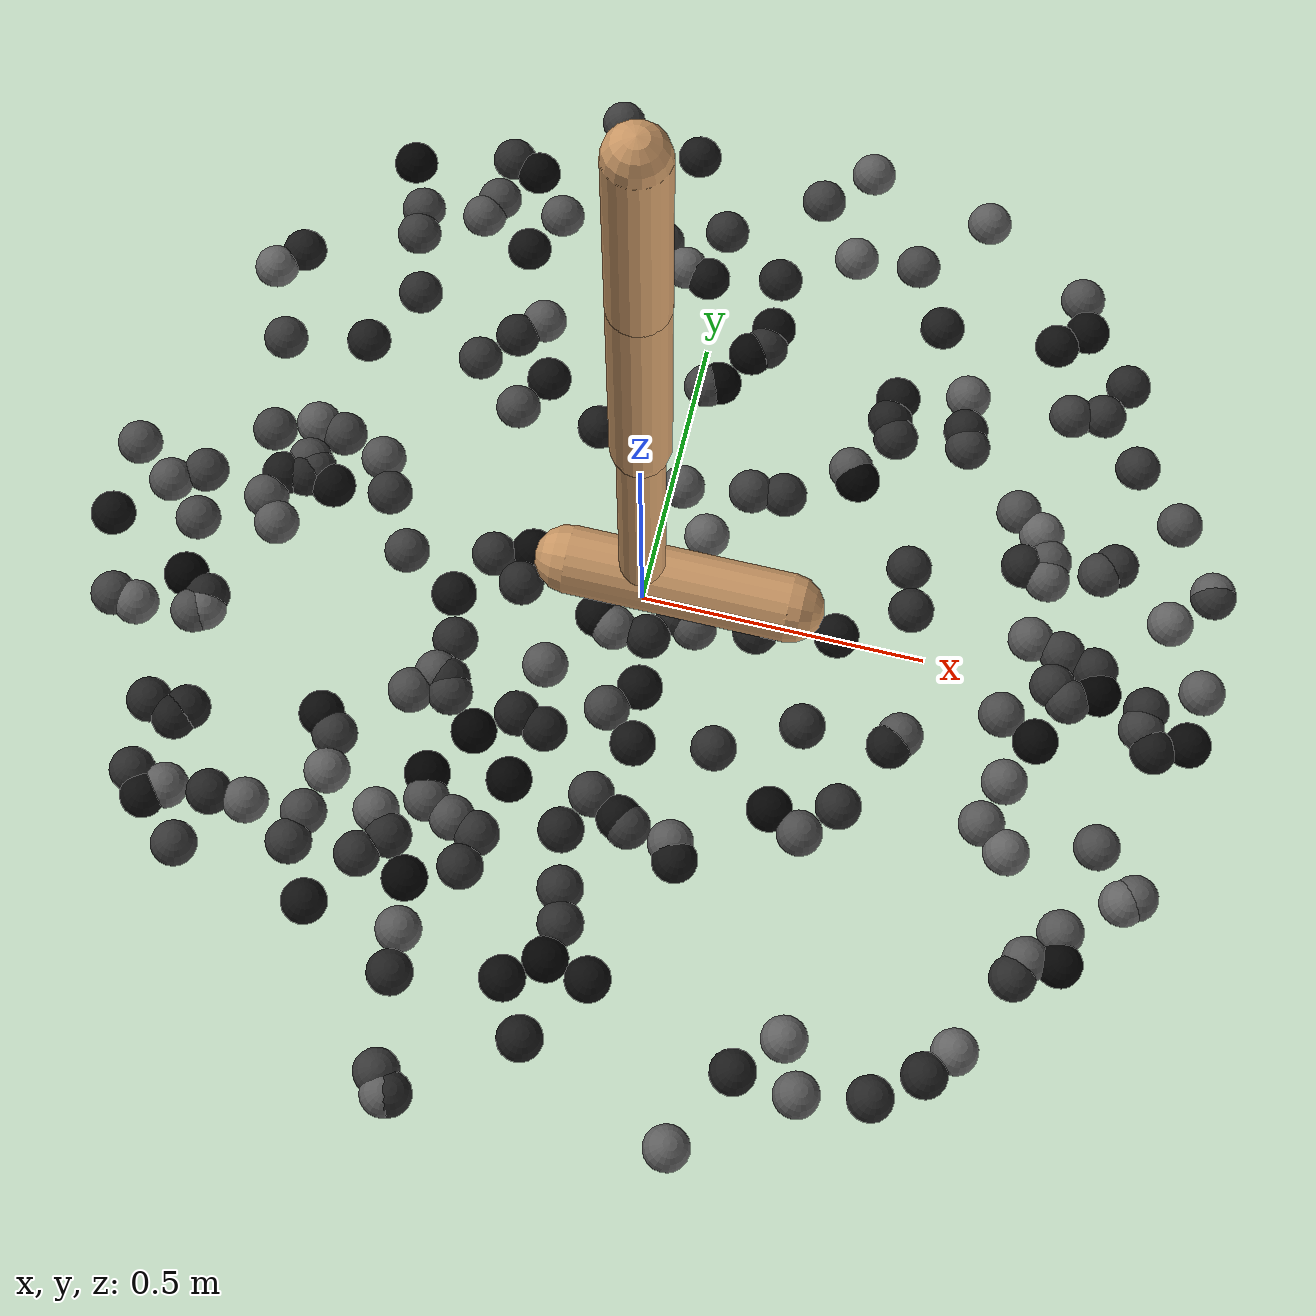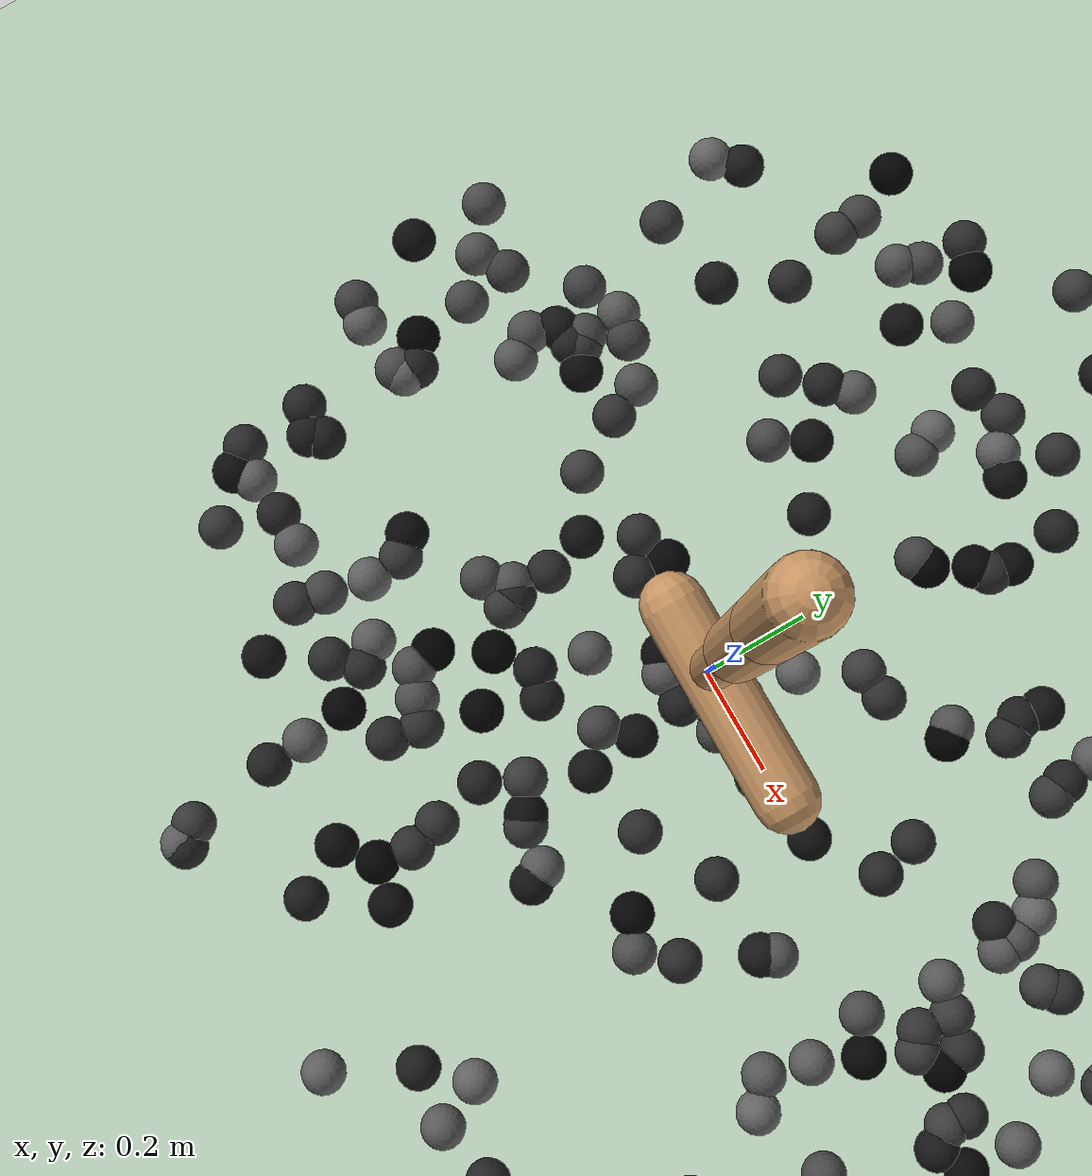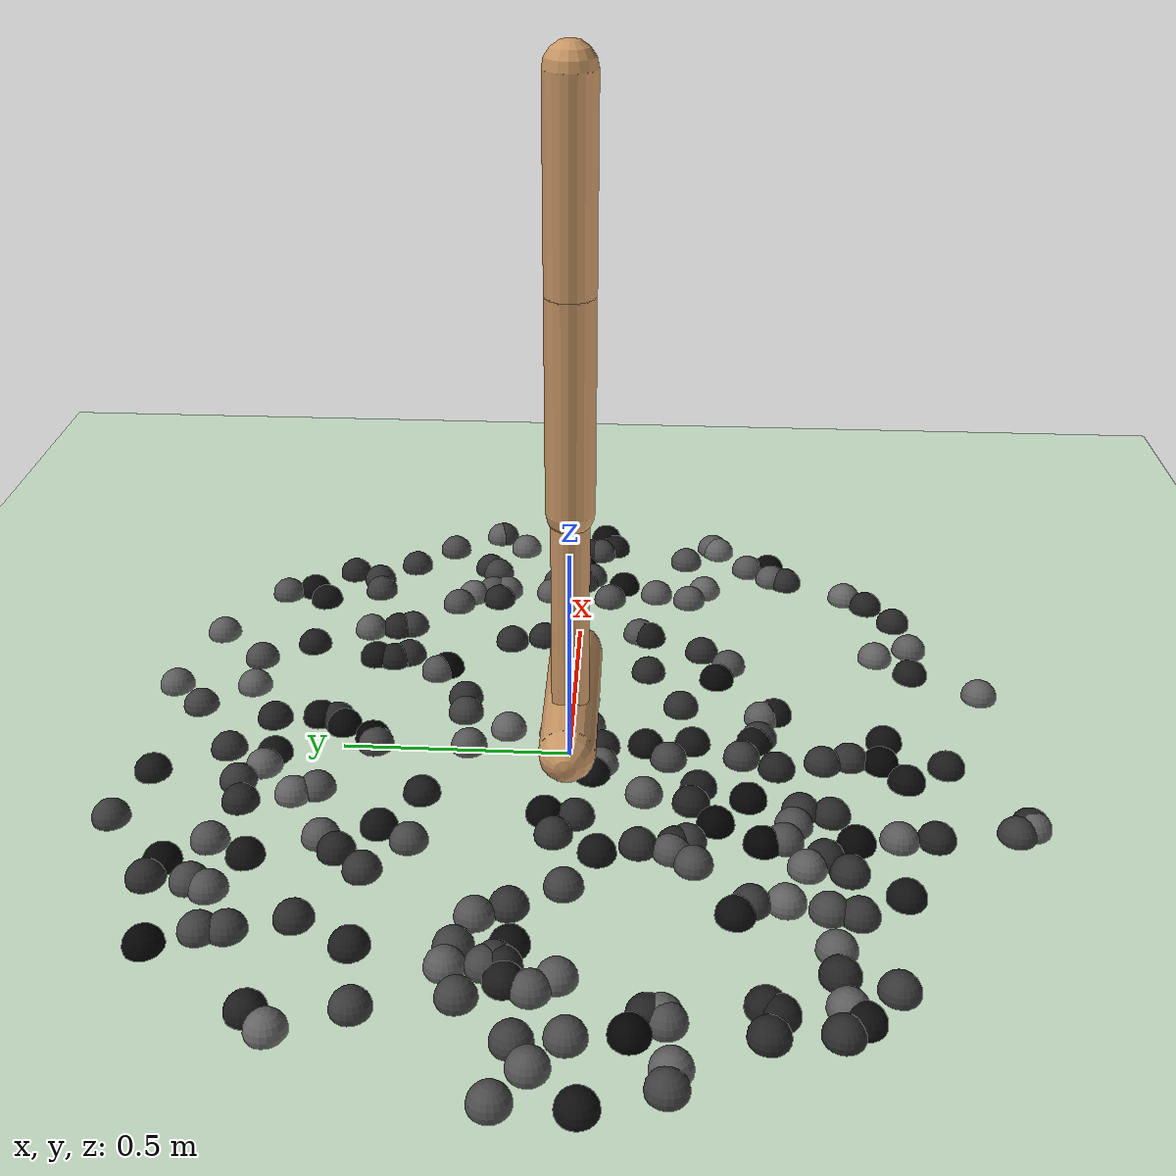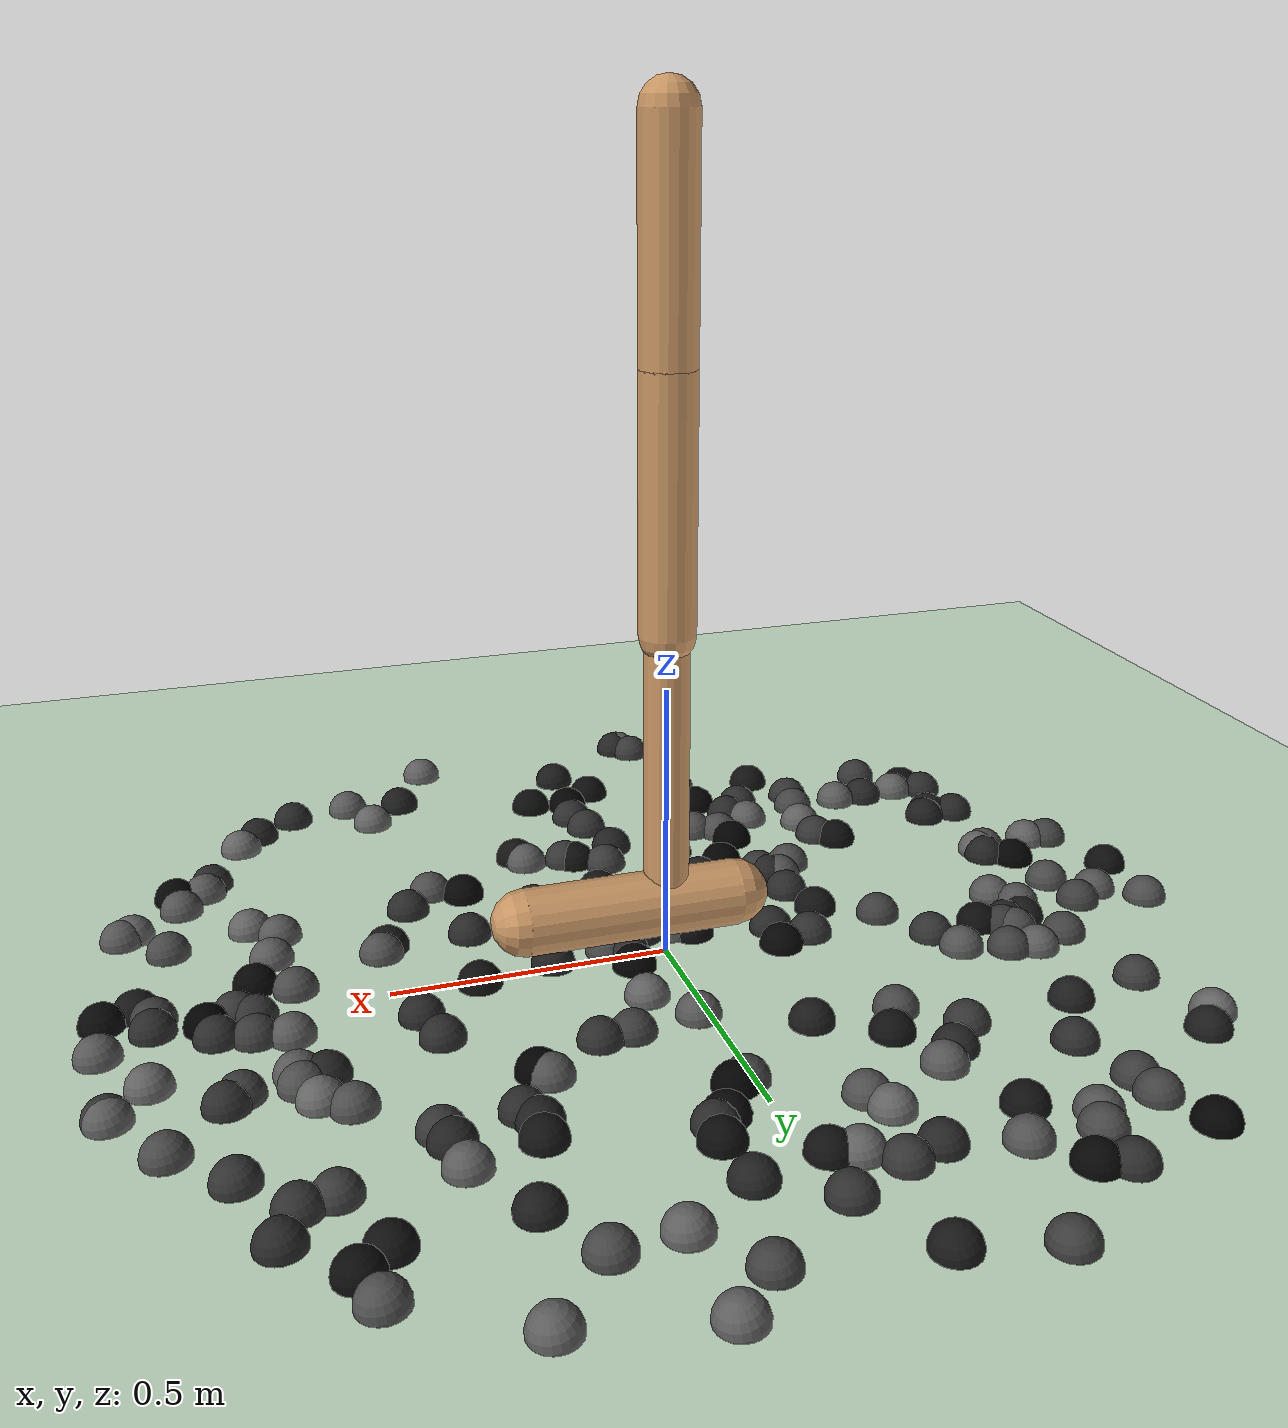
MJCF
<mujoco model="hopper">
  <compiler angle="degree" inertiafromgeom="true"/>
  <default>
    <joint armature="1" damping="1" limited="true"/>
    <geom conaffinity="1" condim="1" contype="1" margin="0.001" material="geom" rgba="0.8 0.6 .4 1" solimp=".8 .8 .01" solref=".02 1"/>
    <motor ctrllimited="true" ctrlrange="-.4 .4"/>
  </default>
  <option integrator="RK4" timestep="0.002"/>
  <visual>
    <map znear="0.02"/>
  </visual>
  <worldbody>
    <light pos="0 0 .6"/>
    <camera name="closeup" pos="0 -3 2" xyaxes="1 0 0 0 1 2"/>
     <!-- Start -->
      <body name="sand_0.06816542371682215_-0.016728379332936243" pos="0.06816542371682215 -0.016728379332936243 0.001">
 <joint name="ball\_jointsand_0.06816542371682215_-0.016728379332936243" type="free" damping="0.9" stiffness="1.2" />
<geom name="ball\_geomsand_0.06816542371682215_-0.016728379332936243" size="0.04" rgba="0.16214803398407904 0.16214803398407904 0.16214803398407904 1.0" type="sphere" density="100" friction="0.5" euler="0 10 0"/>
</body>
<body name="sand_0.012223042342909635_0.4310658824315244" pos="0.012223042342909635 0.4310658824315244 0.001">
 <joint name="ball\_jointsand_0.012223042342909635_0.4310658824315244" type="free" damping="0.9" stiffness="1.2" />
<geom name="ball\_geomsand_0.012223042342909635_0.4310658824315244" size="0.04" rgba="0.26079525470510645 0.26079525470510645 0.26079525470510645 1.0" type="sphere" density="100" friction="0.5" euler="0 10 0"/>
</body>
<body name="sand_0.7738694523764683_-0.48707793179265657" pos="0.7738694523764683 -0.48707793179265657 0.001">
 <joint name="ball\_jointsand_0.7738694523764683_-0.48707793179265657" type="free" damping="0.9" stiffness="1.2" />
<geom name="ball\_geomsand_0.7738694523764683_-0.48707793179265657" size="0.04" rgba="0.340284642626535 0.340284642626535 0.340284642626535 1.0" type="sphere" density="100" friction="0.5" euler="0 10 0"/>
</body>
<body name="sand_-0.034271967514992646_0.6460535169118743" pos="-0.034271967514992646 0.6460535169118743 0.001">
 <joint name="ball\_jointsand_-0.034271967514992646_0.6460535169118743" type="free" damping="0.9" stiffness="1.2" />
<geom name="ball\_geomsand_-0.034271967514992646_0.6460535169118743" size="0.04" rgba="0.06810607800661393 0.06810607800661393 0.06810607800661393 1.0" type="sphere" density="100" friction="0.5" euler="0 10 0"/>
</body>
<body name="sand_0.18439003629170256_-0.24451074060731462" pos="0.18439003629170256 -0.24451074060731462 0.001">
 <joint name="ball\_jointsand_0.18439003629170256_-0.24451074060731462" type="free" damping="0.9" stiffness="1.2" />
<geom name="ball\_geomsand_0.18439003629170256_-0.24451074060731462" size="0.04" rgba="0.17770961288876813 0.17770961288876813 0.17770961288876813 1.0" type="sphere" density="100" friction="0.5" euler="0 10 0"/>
</body>
<body name="sand_-0.5389165111698566_0.4948191085443578" pos="-0.5389165111698566 0.4948191085443578 0.001">
 <joint name="ball\_jointsand_-0.5389165111698566_0.4948191085443578" type="free" damping="0.9" stiffness="1.2" />
<geom name="ball\_geomsand_-0.5389165111698566_0.4948191085443578" size="0.04" rgba="0.1732714699454055 0.1732714699454055 0.1732714699454055 1.0" type="sphere" density="100" friction="0.5" euler="0 10 0"/>
</body>
<body name="sand_-0.5135568648479014_0.15464671258531046" pos="-0.5135568648479014 0.15464671258531046 0.001">
 <joint name="ball\_jointsand_-0.5135568648479014_0.15464671258531046" type="free" damping="0.9" stiffness="1.2" />
<geom name="ball\_geomsand_-0.5135568648479014_0.15464671258531046" size="0.04" rgba="0.3254127407241618 0.3254127407241618 0.3254127407241618 1.0" type="sphere" density="100" friction="0.5" euler="0 10 0"/>
</body>
<body name="sand_-0.009609705853155397_-0.8141400454610382" pos="-0.009609705853155397 -0.8141400454610382 0.001">
 <joint name="ball\_jointsand_-0.009609705853155397_-0.8141400454610382" type="free" damping="0.9" stiffness="1.2" />
<geom name="ball\_geomsand_-0.009609705853155397_-0.8141400454610382" size="0.04" rgba="0.10256555792335549 0.10256555792335549 0.10256555792335549 1.0" type="sphere" density="100" friction="0.5" euler="0 10 0"/>
</body>
<body name="sand_-0.7127358571629072_-0.38397089495430253" pos="-0.7127358571629072 -0.38397089495430253 0.001">
 <joint name="ball\_jointsand_-0.7127358571629072_-0.38397089495430253" type="free" damping="0.9" stiffness="1.2" />
<geom name="ball\_geomsand_-0.7127358571629072_-0.38397089495430253" size="0.04" rgba="0.11723249244011838 0.11723249244011838 0.11723249244011838 1.0" type="sphere" density="100" friction="0.5" euler="0 10 0"/>
</body>
<body name="sand_0.9134671367419883_-0.3533864032859054" pos="0.9134671367419883 -0.3533864032859054 0.001">
 <joint name="ball\_jointsand_0.9134671367419883_-0.3533864032859054" type="free" damping="0.9" stiffness="1.2" />
<geom name="ball\_geomsand_0.9134671367419883_-0.3533864032859054" size="0.04" rgba="0.3981467787746726 0.3981467787746726 0.3981467787746726 1.0" type="sphere" density="100" friction="0.5" euler="0 10 0"/>
</body>
<body name="sand_-0.2979879511362069_-0.1533316890387103" pos="-0.2979879511362069 -0.1533316890387103 0.001">
 <joint name="ball\_jointsand_-0.2979879511362069_-0.1533316890387103" type="free" damping="0.9" stiffness="1.2" />
<geom name="ball\_geomsand_-0.2979879511362069_-0.1533316890387103" size="0.04" rgba="0.16972094365406243 0.16972094365406243 0.16972094365406243 1.0" type="sphere" density="100" friction="0.5" euler="0 10 0"/>
</body>
<body name="sand_0.3547870067089161_0.48636972963972924" pos="0.3547870067089161 0.48636972963972924 0.001">
 <joint name="ball\_jointsand_0.3547870067089161_0.48636972963972924" type="free" damping="0.9" stiffness="1.2" />
<geom name="ball\_geomsand_0.3547870067089161_0.48636972963972924" size="0.04" rgba="0.07446784188106599 0.07446784188106599 0.07446784188106599 1.0" type="sphere" density="100" friction="0.5" euler="0 10 0"/>
</body>
<body name="sand_-0.6267439583704411_0.10462094465998872" pos="-0.6267439583704411 0.10462094465998872 0.001">
 <joint name="ball\_jointsand_-0.6267439583704411_0.10462094465998872" type="free" damping="0.9" stiffness="1.2" />
<geom name="ball\_geomsand_-0.6267439583704411_0.10462094465998872" size="0.04" rgba="0.21531781687566987 0.21531781687566987 0.21531781687566987 1.0" type="sphere" density="100" friction="0.5" euler="0 10 0"/>
</body>
<body name="sand_0.9164109522228671_-0.07416029031331434" pos="0.9164109522228671 -0.07416029031331434 0.001">
 <joint name="ball\_jointsand_0.9164109522228671_-0.07416029031331434" type="free" damping="0.9" stiffness="1.2" />
<geom name="ball\_geomsand_0.9164109522228671_-0.07416029031331434" size="0.04" rgba="0.09185677587482416 0.09185677587482416 0.09185677587482416 1.0" type="sphere" density="100" friction="0.5" euler="0 10 0"/>
</body>
<body name="sand_-0.6202911990620374_0.7583408904808623" pos="-0.6202911990620374 0.7583408904808623 0.001">
 <joint name="ball\_jointsand_-0.6202911990620374_0.7583408904808623" type="free" damping="0.9" stiffness="1.2" />
<geom name="ball\_geomsand_-0.6202911990620374_0.7583408904808623" size="0.04" rgba="0.012716470486801823 0.012716470486801823 0.012716470486801823 1.0" type="sphere" density="100" friction="0.5" euler="0 10 0"/>
</body>
<body name="sand_0.7065208288556968_-0.31089998326943336" pos="0.7065208288556968 -0.31089998326943336 0.001">
 <joint name="ball\_jointsand_0.7065208288556968_-0.31089998326943336" type="free" damping="0.9" stiffness="1.2" />
<geom name="ball\_geomsand_0.7065208288556968_-0.31089998326943336" size="0.04" rgba="0.3951774268858908 0.3951774268858908 0.3951774268858908 1.0" type="sphere" density="100" friction="0.5" euler="0 10 0"/>
</body>
<body name="sand_0.6498272215569804_-0.7185194416490602" pos="0.6498272215569804 -0.7185194416490602 0.001">
 <joint name="ball\_jointsand_0.6498272215569804_-0.7185194416490602" type="free" damping="0.9" stiffness="1.2" />
<geom name="ball\_geomsand_0.6498272215569804_-0.7185194416490602" size="0.04" rgba="0.12859951141211498 0.12859951141211498 0.12859951141211498 1.0" type="sphere" density="100" friction="0.5" euler="0 10 0"/>
</body>
<body name="sand_0.344435606374416_0.00867627229868501" pos="0.344435606374416 0.00867627229868501 0.001">
 <joint name="ball\_jointsand_0.344435606374416_0.00867627229868501" type="free" damping="0.9" stiffness="1.2" />
<geom name="ball\_geomsand_0.344435606374416_0.00867627229868501" size="0.04" rgba="0.06216763803616154 0.06216763803616154 0.06216763803616154 1.0" type="sphere" density="100" friction="0.5" euler="0 10 0"/>
</body>
<body name="sand_-0.567581130006574_-0.522709432567788" pos="-0.567581130006574 -0.522709432567788 0.001">
 <joint name="ball\_jointsand_-0.567581130006574_-0.522709432567788" type="free" damping="0.9" stiffness="1.2" />
<geom name="ball\_geomsand_-0.567581130006574_-0.522709432567788" size="0.04" rgba="0.35901463736123784 0.35901463736123784 0.35901463736123784 1.0" type="sphere" density="100" friction="0.5" euler="0 10 0"/>
</body>
<body name="sand_0.034735400162935644_-0.16558164836198114" pos="0.034735400162935644 -0.16558164836198114 0.001">
 <joint name="ball\_jointsand_0.034735400162935644_-0.16558164836198114" type="free" damping="0.9" stiffness="1.2" />
<geom name="ball\_geomsand_0.034735400162935644_-0.16558164836198114" size="0.04" rgba="0.062613233642081 0.062613233642081 0.062613233642081 1.0" type="sphere" density="100" friction="0.5" euler="0 10 0"/>
</body>
<body name="sand_0.6651409531907008_0.5252227126510497" pos="0.6651409531907008 0.5252227126510497 0.001">
 <joint name="ball\_jointsand_0.6651409531907008_0.5252227126510497" type="free" damping="0.9" stiffness="1.2" />
<geom name="ball\_geomsand_0.6651409531907008_0.5252227126510497" size="0.04" rgba="0.23233862637148875 0.23233862637148875 0.23233862637148875 1.0" type="sphere" density="100" friction="0.5" euler="0 10 0"/>
</body>
<body name="sand_0.6137319576471838_0.6592100351736228" pos="0.6137319576471838 0.6592100351736228 0.001">
 <joint name="ball\_jointsand_0.6137319576471838_0.6592100351736228" type="free" damping="0.9" stiffness="1.2" />
<geom name="ball\_geomsand_0.6137319576471838_0.6592100351736228" size="0.04" rgba="0.06653200501207004 0.06653200501207004 0.06653200501207004 1.0" type="sphere" density="100" friction="0.5" euler="0 10 0"/>
</body>
<body name="sand_-0.07917623243879598_0.659149385586077" pos="-0.07917623243879598 0.659149385586077 0.001">
 <joint name="ball\_jointsand_-0.07917623243879598_0.659149385586077" type="free" damping="0.9" stiffness="1.2" />
<geom name="ball\_geomsand_-0.07917623243879598_0.659149385586077" size="0.04" rgba="0.3808350586899145 0.3808350586899145 0.3808350586899145 1.0" type="sphere" density="100" friction="0.5" euler="0 10 0"/>
</body>
<body name="sand_-0.26447664123113457_0.9356490613434546" pos="-0.26447664123113457 0.9356490613434546 0.001">
 <joint name="ball\_jointsand_-0.26447664123113457_0.9356490613434546" type="free" damping="0.9" stiffness="1.2" />
<geom name="ball\_geomsand_-0.26447664123113457_0.9356490613434546" size="0.04" rgba="0.23881040537154496 0.23881040537154496 0.23881040537154496 1.0" type="sphere" density="100" friction="0.5" euler="0 10 0"/>
</body>
<body name="sand_-0.4476136924616969_-0.43862190691389114" pos="-0.4476136924616969 -0.43862190691389114 0.001">
 <joint name="ball\_jointsand_-0.4476136924616969_-0.43862190691389114" type="free" damping="0.9" stiffness="1.2" />
<geom name="ball\_geomsand_-0.4476136924616969_-0.43862190691389114" size="0.04" rgba="0.3809710632780673 0.3809710632780673 0.3809710632780673 1.0" type="sphere" density="100" friction="0.5" euler="0 10 0"/>
</body>
<body name="sand_0.3174311471796693_0.309858576520989" pos="0.3174311471796693 0.309858576520989 0.001">
 <joint name="ball\_jointsand_0.3174311471796693_0.309858576520989" type="free" damping="0.9" stiffness="1.2" />
<geom name="ball\_geomsand_0.3174311471796693_0.309858576520989" size="0.04" rgba="0.002708235080869326 0.002708235080869326 0.002708235080869326 1.0" type="sphere" density="100" friction="0.5" euler="0 10 0"/>
</body>
<body name="sand_-0.3265442428252053_0.7121508573896898" pos="-0.3265442428252053 0.7121508573896898 0.001">
 <joint name="ball\_jointsand_-0.3265442428252053_0.7121508573896898" type="free" damping="0.9" stiffness="1.2" />
<geom name="ball\_geomsand_-0.3265442428252053_0.7121508573896898" size="0.04" rgba="0.32331392104120504 0.32331392104120504 0.32331392104120504 1.0" type="sphere" density="100" friction="0.5" euler="0 10 0"/>
</body>
<body name="sand_-0.8140302362550746_0.0577376895925666" pos="-0.8140302362550746 0.0577376895925666 0.001">
 <joint name="ball\_jointsand_-0.8140302362550746_0.0577376895925666" type="free" damping="0.9" stiffness="1.2" />
<geom name="ball\_geomsand_-0.8140302362550746_0.0577376895925666" size="0.04" rgba="0.24241929531416662 0.24241929531416662 0.24241929531416662 1.0" type="sphere" density="100" friction="0.5" euler="0 10 0"/>
</body>
<body name="sand_-0.6629457729216462_-0.6247326422098263" pos="-0.6629457729216462 -0.6247326422098263 0.001">
 <joint name="ball\_jointsand_-0.6629457729216462_-0.6247326422098263" type="free" damping="0.9" stiffness="1.2" />
<geom name="ball\_geomsand_-0.6629457729216462_-0.6247326422098263" size="0.04" rgba="0.21841950345234015 0.21841950345234015 0.21841950345234015 1.0" type="sphere" density="100" friction="0.5" euler="0 10 0"/>
</body>
<body name="sand_-0.036271892629573026_-0.06702613139396833" pos="-0.036271892629573026 -0.06702613139396833 0.001">
 <joint name="ball\_jointsand_-0.036271892629573026_-0.06702613139396833" type="free" damping="0.9" stiffness="1.2" />
<geom name="ball\_geomsand_-0.036271892629573026_-0.06702613139396833" size="0.04" rgba="0.3459542671186058 0.3459542671186058 0.3459542671186058 1.0" type="sphere" density="100" friction="0.5" euler="0 10 0"/>
</body>
<body name="sand_-0.5860636281568692_0.08133366243420403" pos="-0.5860636281568692 0.08133366243420403 0.001">
 <joint name="ball\_jointsand_-0.5860636281568692_0.08133366243420403" type="free" damping="0.9" stiffness="1.2" />
<geom name="ball\_geomsand_-0.5860636281568692_0.08133366243420403" size="0.04" rgba="0.04900139630675544 0.04900139630675544 0.04900139630675544 1.0" type="sphere" density="100" friction="0.5" euler="0 10 0"/>
</body>
<body name="sand_-0.2910330233044219_-0.22829547143980455" pos="-0.2910330233044219 -0.22829547143980455 0.001">
 <joint name="ball\_jointsand_-0.2910330233044219_-0.22829547143980455" type="free" damping="0.9" stiffness="1.2" />
<geom name="ball\_geomsand_-0.2910330233044219_-0.22829547143980455" size="0.04" rgba="0.14349667675699215 0.14349667675699215 0.14349667675699215 1.0" type="sphere" density="100" friction="0.5" euler="0 10 0"/>
</body>
<body name="sand_-0.47573711169495875_-0.5755917163495692" pos="-0.47573711169495875 -0.5755917163495692 0.001">
 <joint name="ball\_jointsand_-0.47573711169495875_-0.5755917163495692" type="free" damping="0.9" stiffness="1.2" />
<geom name="ball\_geomsand_-0.47573711169495875_-0.5755917163495692" size="0.04" rgba="0.20368281928620902 0.20368281928620902 0.20368281928620902 1.0" type="sphere" density="100" friction="0.5" euler="0 10 0"/>
</body>
<body name="sand_-0.3478607528641395_-0.2629654873000856" pos="-0.3478607528641395 -0.2629654873000856 0.001">
 <joint name="ball\_jointsand_-0.3478607528641395_-0.2629654873000856" type="free" damping="0.9" stiffness="1.2" />
<geom name="ball\_geomsand_-0.3478607528641395_-0.2629654873000856" size="0.04" rgba="0.29009451247159584 0.29009451247159584 0.29009451247159584 1.0" type="sphere" density="100" friction="0.5" euler="0 10 0"/>
</body>
<body name="sand_0.19771874597285446_0.25171641608333395" pos="0.19771874597285446 0.25171641608333395 0.001">
 <joint name="ball\_jointsand_0.19771874597285446_0.25171641608333395" type="free" damping="0.9" stiffness="1.2" />
<geom name="ball\_geomsand_0.19771874597285446_0.25171641608333395" size="0.04" rgba="0.18088063959062659 0.18088063959062659 0.18088063959062659 1.0" type="sphere" density="100" friction="0.5" euler="0 10 0"/>
</body>
<body name="sand_-0.2676628562357357_-0.5925951565798796" pos="-0.2676628562357357 -0.5925951565798796 0.001">
 <joint name="ball\_jointsand_-0.2676628562357357_-0.5925951565798796" type="free" damping="0.9" stiffness="1.2" />
<geom name="ball\_geomsand_-0.2676628562357357_-0.5925951565798796" size="0.04" rgba="0.016089338679138622 0.016089338679138622 0.016089338679138622 1.0" type="sphere" density="100" friction="0.5" euler="0 10 0"/>
</body>
<body name="sand_0.8541578843816902_-0.2661333898401764" pos="0.8541578843816902 -0.2661333898401764 0.001">
 <joint name="ball\_jointsand_0.8541578843816902_-0.2661333898401764" type="free" damping="0.9" stiffness="1.2" />
<geom name="ball\_geomsand_0.8541578843816902_-0.2661333898401764" size="0.04" rgba="0.29152832114843846 0.29152832114843846 0.29152832114843846 1.0" type="sphere" density="100" friction="0.5" euler="0 10 0"/>
</body>
<body name="sand_0.7944286747755693_0.25312941753815826" pos="0.7944286747755693 0.25312941753815826 0.001">
 <joint name="ball\_jointsand_0.7944286747755693_0.25312941753815826" type="free" damping="0.9" stiffness="1.2" />
<geom name="ball\_geomsand_0.7944286747755693_0.25312941753815826" size="0.04" rgba="0.1764627095148319 0.1764627095148319 0.1764627095148319 1.0" type="sphere" density="100" friction="0.5" euler="0 10 0"/>
</body>
<body name="sand_0.07462292954374486_-0.6909266110248492" pos="0.07462292954374486 -0.6909266110248492 0.001">
 <joint name="ball\_jointsand_0.07462292954374486_-0.6909266110248492" type="free" damping="0.9" stiffness="1.2" />
<geom name="ball\_geomsand_0.07462292954374486_-0.6909266110248492" size="0.04" rgba="0.05255505616213916 0.05255505616213916 0.05255505616213916 1.0" type="sphere" density="100" friction="0.5" euler="0 10 0"/>
</body>
<body name="sand_0.8063148211905775_0.00795922767215874" pos="0.8063148211905775 0.00795922767215874 0.001">
 <joint name="ball\_jointsand_0.8063148211905775_0.00795922767215874" type="free" damping="0.9" stiffness="1.2" />
<geom name="ball\_geomsand_0.8063148211905775_0.00795922767215874" size="0.04" rgba="0.00016032137759354194 0.00016032137759354194 0.00016032137759354194 1.0" type="sphere" density="100" friction="0.5" euler="0 10 0"/>
</body>
<body name="sand_0.006895137071451391_-0.6081180028387918" pos="0.006895137071451391 -0.6081180028387918 0.001">
 <joint name="ball\_jointsand_0.006895137071451391_-0.6081180028387918" type="free" damping="0.9" stiffness="1.2" />
<geom name="ball\_geomsand_0.006895137071451391_-0.6081180028387918" size="0.04" rgba="0.18474453699074608 0.18474453699074608 0.18474453699074608 1.0" type="sphere" density="100" friction="0.5" euler="0 10 0"/>
</body>
<body name="sand_-0.8693389963700748_0.02538030586824643" pos="-0.8693389963700748 0.02538030586824643 0.001">
 <joint name="ball\_jointsand_-0.8693389963700748_0.02538030586824643" type="free" damping="0.9" stiffness="1.2" />
<geom name="ball\_geomsand_-0.8693389963700748_0.02538030586824643" size="0.04" rgba="0.32506499972060426 0.32506499972060426 0.32506499972060426 1.0" type="sphere" density="100" friction="0.5" euler="0 10 0"/>
</body>
<body name="sand_0.017901406713082314_0.22475785795131242" pos="0.017901406713082314 0.22475785795131242 0.001">
 <joint name="ball\_jointsand_0.017901406713082314_0.22475785795131242" type="free" damping="0.9" stiffness="1.2" />
<geom name="ball\_geomsand_0.017901406713082314_0.22475785795131242" size="0.04" rgba="0.33976541692717155 0.33976541692717155 0.33976541692717155 1.0" type="sphere" density="100" friction="0.5" euler="0 10 0"/>
</body>
<body name="sand_0.025716309636540084_-0.06943946415419729" pos="0.025716309636540084 -0.06943946415419729 0.001">
 <joint name="ball\_jointsand_0.025716309636540084_-0.06943946415419729" type="free" damping="0.9" stiffness="1.2" />
<geom name="ball\_geomsand_0.025716309636540084_-0.06943946415419729" size="0.04" rgba="0.12658178969389144 0.12658178969389144 0.12658178969389144 1.0" type="sphere" density="100" friction="0.5" euler="0 10 0"/>
</body>
<body name="sand_-0.1945596791768748_-0.9539672588680729" pos="-0.1945596791768748 -0.9539672588680729 0.001">
 <joint name="ball\_jointsand_-0.1945596791768748_-0.9539672588680729" type="free" damping="0.9" stiffness="1.2" />
<geom name="ball\_geomsand_-0.1945596791768748_-0.9539672588680729" size="0.04" rgba="0.14458428224820943 0.14458428224820943 0.14458428224820943 1.0" type="sphere" density="100" friction="0.5" euler="0 10 0"/>
</body>
<body name="sand_-0.6318763083418081_-0.5225535100063265" pos="-0.6318763083418081 -0.5225535100063265 0.001">
 <joint name="ball\_jointsand_-0.6318763083418081_-0.5225535100063265" type="free" damping="0.9" stiffness="1.2" />
<geom name="ball\_geomsand_-0.6318763083418081_-0.5225535100063265" size="0.04" rgba="0.14393605604870283 0.14393605604870283 0.14393605604870283 1.0" type="sphere" density="100" friction="0.5" euler="0 10 0"/>
</body>
<body name="sand_-0.7415198037690346_-0.17455151386299447" pos="-0.7415198037690346 -0.17455151386299447 0.001">
 <joint name="ball\_jointsand_-0.7415198037690346_-0.17455151386299447" type="free" damping="0.9" stiffness="1.2" />
<geom name="ball\_geomsand_-0.7415198037690346_-0.17455151386299447" size="0.04" rgba="0.13763042228368325 0.13763042228368325 0.13763042228368325 1.0" type="sphere" density="100" friction="0.5" euler="0 10 0"/>
</body>
<body name="sand_-0.8011650748382846_-0.034997128283096646" pos="-0.8011650748382846 -0.034997128283096646 0.001">
 <joint name="ball\_jointsand_-0.8011650748382846_-0.034997128283096646" type="free" damping="0.9" stiffness="1.2" />
<geom name="ball\_geomsand_-0.8011650748382846_-0.034997128283096646" size="0.04" rgba="0.28914327808944895 0.28914327808944895 0.28914327808944895 1.0" type="sphere" density="100" friction="0.5" euler="0 10 0"/>
</body>
<body name="sand_-0.6777102519222258_0.08396127227523134" pos="-0.6777102519222258 0.08396127227523134 0.001">
 <joint name="ball\_jointsand_-0.6777102519222258_0.08396127227523134" type="free" damping="0.9" stiffness="1.2" />
<geom name="ball\_geomsand_-0.6777102519222258_0.08396127227523134" size="0.04" rgba="0.09525015552727428 0.09525015552727428 0.09525015552727428 1.0" type="sphere" density="100" friction="0.5" euler="0 10 0"/>
</body>
<body name="sand_0.4415523951248604_0.16500005077715416" pos="0.4415523951248604 0.16500005077715416 0.001">
 <joint name="ball\_jointsand_0.4415523951248604_0.16500005077715416" type="free" damping="0.9" stiffness="1.2" />
<geom name="ball\_geomsand_0.4415523951248604_0.16500005077715416" size="0.04" rgba="0.1708412179326059 0.1708412179326059 0.1708412179326059 1.0" type="sphere" density="100" friction="0.5" euler="0 10 0"/>
</body>
<body name="sand_-0.48546379905665615_-0.33975954952147525" pos="-0.48546379905665615 -0.33975954952147525 0.001">
 <joint name="ball\_jointsand_-0.48546379905665615_-0.33975954952147525" type="free" damping="0.9" stiffness="1.2" />
<geom name="ball\_geomsand_-0.48546379905665615_-0.33975954952147525" size="0.04" rgba="0.046995651658526955 0.046995651658526955 0.046995651658526955 1.0" type="sphere" density="100" friction="0.5" euler="0 10 0"/>
</body>
<body name="sand_0.7212217147492401_0.5384085181781006" pos="0.7212217147492401 0.5384085181781006 0.001">
 <joint name="ball\_jointsand_0.7212217147492401_0.5384085181781006" type="free" damping="0.9" stiffness="1.2" />
<geom name="ball\_geomsand_0.7212217147492401_0.5384085181781006" size="0.04" rgba="0.19249212847572147 0.19249212847572147 0.19249212847572147 1.0" type="sphere" density="100" friction="0.5" euler="0 10 0"/>
</body>
<body name="sand_-0.4670742841190753_0.6785183585436443" pos="-0.4670742841190753 0.6785183585436443 0.001">
 <joint name="ball\_jointsand_-0.4670742841190753_0.6785183585436443" type="free" damping="0.9" stiffness="1.2" />
<geom name="ball\_geomsand_-0.4670742841190753_0.6785183585436443" size="0.04" rgba="0.3255093577706988 0.3255093577706988 0.3255093577706988 1.0" type="sphere" density="100" friction="0.5" euler="0 10 0"/>
</body>
<body name="sand_-0.26625394481275994_0.37784764993795766" pos="-0.26625394481275994 0.37784764993795766 0.001">
 <joint name="ball\_jointsand_-0.26625394481275994_0.37784764993795766" type="free" damping="0.9" stiffness="1.2" />
<geom name="ball\_geomsand_-0.26625394481275994_0.37784764993795766" size="0.04" rgba="0.06840772337796355 0.06840772337796355 0.06840772337796355 1.0" type="sphere" density="100" friction="0.5" euler="0 10 0"/>
</body>
<body name="sand_-0.594093664835774_0.18456168968456949" pos="-0.594093664835774 0.18456168968456949 0.001">
 <joint name="ball\_jointsand_-0.594093664835774_0.18456168968456949" type="free" damping="0.9" stiffness="1.2" />
<geom name="ball\_geomsand_-0.594093664835774_0.18456168968456949" size="0.04" rgba="0.2504723527384351 0.2504723527384351 0.2504723527384351 1.0" type="sphere" density="100" friction="0.5" euler="0 10 0"/>
</body>
<body name="sand_-0.21806350437708383_-0.47048628024417566" pos="-0.21806350437708383 -0.47048628024417566 0.001">
 <joint name="ball\_jointsand_-0.21806350437708383_-0.47048628024417566" type="free" damping="0.9" stiffness="1.2" />
<geom name="ball\_geomsand_-0.21806350437708383_-0.47048628024417566" size="0.04" rgba="0.3060540716079888 0.3060540716079888 0.3060540716079888 1.0" type="sphere" density="100" friction="0.5" euler="0 10 0"/>
</body>
<body name="sand_0.05703405808435048_-0.4044410180850521" pos="0.05703405808435048 -0.4044410180850521 0.001">
 <joint name="ball\_jointsand_0.05703405808435048_-0.4044410180850521" type="free" damping="0.9" stiffness="1.2" />
<geom name="ball\_geomsand_0.05703405808435048_-0.4044410180850521" size="0.04" rgba="0.056095910862826996 0.056095910862826996 0.056095910862826996 1.0" type="sphere" density="100" friction="0.5" euler="0 10 0"/>
</body>
<body name="sand_0.571831219503109_-0.7771384210433517" pos="0.571831219503109 -0.7771384210433517 0.001">
 <joint name="ball\_jointsand_0.571831219503109_-0.7771384210433517" type="free" damping="0.9" stiffness="1.2" />
<geom name="ball\_geomsand_0.571831219503109_-0.7771384210433517" size="0.04" rgba="0.1513561557421583 0.1513561557421583 0.1513561557421583 1.0" type="sphere" density="100" friction="0.5" euler="0 10 0"/>
</body>
<body name="sand_0.6565674852545774_-0.2702700466682682" pos="0.6565674852545774 -0.2702700466682682 0.001">
 <joint name="ball\_jointsand_0.6565674852545774_-0.2702700466682682" type="free" damping="0.9" stiffness="1.2" />
<geom name="ball\_geomsand_0.6565674852545774_-0.2702700466682682" size="0.04" rgba="0.34425019889971353 0.34425019889971353 0.34425019889971353 1.0" type="sphere" density="100" friction="0.5" euler="0 10 0"/>
</body>
<body name="sand_-0.6451770363460712_0.1942603547539936" pos="-0.6451770363460712 0.1942603547539936 0.001">
 <joint name="ball\_jointsand_-0.6451770363460712_0.1942603547539936" type="free" damping="0.9" stiffness="1.2" />
<geom name="ball\_geomsand_-0.6451770363460712_0.1942603547539936" size="0.04" rgba="0.3594611453957908 0.3594611453957908 0.3594611453957908 1.0" type="sphere" density="100" friction="0.5" euler="0 10 0"/>
</body>
<body name="sand_0.13868437702527142_0.24455899287722585" pos="0.13868437702527142 0.24455899287722585 0.001">
 <joint name="ball\_jointsand_0.13868437702527142_0.24455899287722585" type="free" damping="0.9" stiffness="1.2" />
<geom name="ball\_geomsand_0.13868437702527142_0.24455899287722585" size="0.04" rgba="0.2378923559344619 0.2378923559344619 0.2378923559344619 1.0" type="sphere" density="100" friction="0.5" euler="0 10 0"/>
</body>
<body name="sand_-0.5800155185092223_0.6669975667060002" pos="-0.5800155185092223 0.6669975667060002 0.001">
 <joint name="ball\_jointsand_-0.5800155185092223_0.6669975667060002" type="free" damping="0.9" stiffness="1.2" />
<geom name="ball\_geomsand_-0.5800155185092223_0.6669975667060002" size="0.04" rgba="0.26353543751952263 0.26353543751952263 0.26353543751952263 1.0" type="sphere" density="100" friction="0.5" euler="0 10 0"/>
</body>
<body name="sand_0.3354209552337816_0.760796171844269" pos="0.3354209552337816 0.760796171844269 0.001">
 <joint name="ball\_jointsand_0.3354209552337816_0.760796171844269" type="free" damping="0.9" stiffness="1.2" />
<geom name="ball\_geomsand_0.3354209552337816_0.760796171844269" size="0.04" rgba="0.2781271132716147 0.2781271132716147 0.2781271132716147 1.0" type="sphere" density="100" friction="0.5" euler="0 10 0"/>
</body>
<body name="sand_0.04760919816852151_-0.2682135754201197" pos="0.04760919816852151 -0.2682135754201197 0.001">
 <joint name="ball\_jointsand_0.04760919816852151_-0.2682135754201197" type="free" damping="0.9" stiffness="1.2" />
<geom name="ball\_geomsand_0.04760919816852151_-0.2682135754201197" size="0.04" rgba="0.08105193011178131 0.08105193011178131 0.08105193011178131 1.0" type="sphere" density="100" friction="0.5" euler="0 10 0"/>
</body>
<body name="sand_-0.4205947566550142_-0.6713048607418336" pos="-0.4205947566550142 -0.6713048607418336 0.001">
 <joint name="ball\_jointsand_-0.4205947566550142_-0.6713048607418336" type="free" damping="0.9" stiffness="1.2" />
<geom name="ball\_geomsand_-0.4205947566550142_-0.6713048607418336" size="0.04" rgba="0.07083725815680046 0.07083725815680046 0.07083725815680046 1.0" type="sphere" density="100" friction="0.5" euler="0 10 0"/>
</body>
<body name="sand_-0.06829195251818532_-0.050749612393940366" pos="-0.06829195251818532 -0.050749612393940366 0.001">
 <joint name="ball\_jointsand_-0.06829195251818532_-0.050749612393940366" type="free" damping="0.9" stiffness="1.2" />
<geom name="ball\_geomsand_-0.06829195251818532_-0.050749612393940366" size="0.04" rgba="0.04395262787086565 0.04395262787086565 0.04395262787086565 1.0" type="sphere" density="100" friction="0.5" euler="0 10 0"/>
</body>
<body name="sand_0.49003249057486126_-0.14634293034410992" pos="0.49003249057486126 -0.14634293034410992 0.001">
 <joint name="ball\_jointsand_0.49003249057486126_-0.14634293034410992" type="free" damping="0.9" stiffness="1.2" />
<geom name="ball\_geomsand_0.49003249057486126_-0.14634293034410992" size="0.04" rgba="0.31355830954347813 0.31355830954347813 0.31355830954347813 1.0" type="sphere" density="100" friction="0.5" euler="0 10 0"/>
</body>
<body name="sand_-0.2028400512564472_-0.9562045432897165" pos="-0.2028400512564472 -0.9562045432897165 0.001">
 <joint name="ball\_jointsand_-0.2028400512564472_-0.9562045432897165" type="free" damping="0.9" stiffness="1.2" />
<geom name="ball\_geomsand_-0.2028400512564472_-0.9562045432897165" size="0.04" rgba="0.36790208934123103 0.36790208934123103 0.36790208934123103 1.0" type="sphere" density="100" friction="0.5" euler="0 10 0"/>
</body>
<body name="sand_-0.6401819998260685_0.12155526152678826" pos="-0.6401819998260685 0.12155526152678826 0.001">
 <joint name="ball\_jointsand_-0.6401819998260685_0.12155526152678826" type="free" damping="0.9" stiffness="1.2" />
<geom name="ball\_geomsand_-0.6401819998260685_0.12155526152678826" size="0.04" rgba="0.27760447158229495 0.27760447158229495 0.27760447158229495 1.0" type="sphere" density="100" friction="0.5" euler="0 10 0"/>
</body>
<body name="sand_-0.858660153554456_-0.2164663317966272" pos="-0.858660153554456 -0.2164663317966272 0.001">
 <joint name="ball\_jointsand_-0.858660153554456_-0.2164663317966272" type="free" damping="0.9" stiffness="1.2" />
<geom name="ball\_geomsand_-0.858660153554456_-0.2164663317966272" size="0.04" rgba="0.3741997585428811 0.3741997585428811 0.3741997585428811 1.0" type="sphere" density="100" friction="0.5" euler="0 10 0"/>
</body>
<body name="sand_-0.7398807578906191_-0.5544992992285525" pos="-0.7398807578906191 -0.5544992992285525 0.001">
 <joint name="ball\_jointsand_-0.7398807578906191_-0.5544992992285525" type="free" damping="0.9" stiffness="1.2" />
<geom name="ball\_geomsand_-0.7398807578906191_-0.5544992992285525" size="0.04" rgba="0.054904441798273855 0.054904441798273855 0.054904441798273855 1.0" type="sphere" density="100" friction="0.5" euler="0 10 0"/>
</body>
<body name="sand_-0.20078565276800145_0.6805975795424514" pos="-0.20078565276800145 0.6805975795424514 0.001">
 <joint name="ball\_jointsand_-0.20078565276800145_0.6805975795424514" type="free" damping="0.9" stiffness="1.2" />
<geom name="ball\_geomsand_-0.20078565276800145_0.6805975795424514" size="0.04" rgba="0.1496612272919826 0.1496612272919826 0.1496612272919826 1.0" type="sphere" density="100" friction="0.5" euler="0 10 0"/>
</body>
<body name="sand_-0.6637374730732917_-0.011186438037831732" pos="-0.6637374730732917 -0.011186438037831732 0.001">
 <joint name="ball\_jointsand_-0.6637374730732917_-0.011186438037831732" type="free" damping="0.9" stiffness="1.2" />
<geom name="ball\_geomsand_-0.6637374730732917_-0.011186438037831732" size="0.04" rgba="0.34566537809104214 0.34566537809104214 0.34566537809104214 1.0" type="sphere" density="100" friction="0.5" euler="0 10 0"/>
</body>
<body name="sand_-0.4656866262371318_-0.5193585681132002" pos="-0.4656866262371318 -0.5193585681132002 0.001">
 <joint name="ball\_jointsand_-0.4656866262371318_-0.5193585681132002" type="free" damping="0.9" stiffness="1.2" />
<geom name="ball\_geomsand_-0.4656866262371318_-0.5193585681132002" size="0.04" rgba="0.274049345511669 0.274049345511669 0.274049345511669 1.0" type="sphere" density="100" friction="0.5" euler="0 10 0"/>
</body>
<body name="sand_0.7172945793767722_-0.10289564877545354" pos="0.7172945793767722 -0.10289564877545354 0.001">
 <joint name="ball\_jointsand_0.7172945793767722_-0.10289564877545354" type="free" damping="0.9" stiffness="1.2" />
<geom name="ball\_geomsand_0.7172945793767722_-0.10289564877545354" size="0.04" rgba="0.023743585393289603 0.023743585393289603 0.023743585393289603 1.0" type="sphere" density="100" friction="0.5" euler="0 10 0"/>
</body>
<body name="sand_0.34925440590095974_0.4408925201388187" pos="0.34925440590095974 0.4408925201388187 0.001">
 <joint name="ball\_jointsand_0.34925440590095974_0.4408925201388187" type="free" damping="0.9" stiffness="1.2" />
<geom name="ball\_geomsand_0.34925440590095974_0.4408925201388187" size="0.04" rgba="0.12229114546797969 0.12229114546797969 0.12229114546797969 1.0" type="sphere" density="100" friction="0.5" euler="0 10 0"/>
</body>
<body name="sand_0.47555291942905664_-0.1698290294705272" pos="0.47555291942905664 -0.1698290294705272 0.001">
 <joint name="ball\_jointsand_0.47555291942905664_-0.1698290294705272" type="free" damping="0.9" stiffness="1.2" />
<geom name="ball\_geomsand_0.47555291942905664_-0.1698290294705272" size="0.04" rgba="0.09207183166322284 0.09207183166322284 0.09207183166322284 1.0" type="sphere" density="100" friction="0.5" euler="0 10 0"/>
</body>
<body name="sand_0.2675928555125546_-0.934265418892139" pos="0.2675928555125546 -0.934265418892139 0.001">
 <joint name="ball\_jointsand_0.2675928555125546_-0.934265418892139" type="free" damping="0.9" stiffness="1.2" />
<geom name="ball\_geomsand_0.2675928555125546_-0.934265418892139" size="0.04" rgba="0.37924819298543233 0.37924819298543233 0.37924819298543233 1.0" type="sphere" density="100" friction="0.5" euler="0 10 0"/>
</body>
<body name="sand_-0.3061780896640221_0.3103858803603247" pos="-0.3061780896640221 0.3103858803603247 0.001">
 <joint name="ball\_jointsand_-0.3061780896640221_0.3103858803603247" type="free" damping="0.9" stiffness="1.2" />
<geom name="ball\_geomsand_-0.3061780896640221_0.3103858803603247" size="0.04" rgba="0.28486768835378795 0.28486768835378795 0.28486768835378795 1.0" type="sphere" density="100" friction="0.5" euler="0 10 0"/>
</body>
<body name="sand_0.7538365794010039_0.6077493932623611" pos="0.7538365794010039 0.6077493932623611 0.001">
 <joint name="ball\_jointsand_0.7538365794010039_0.6077493932623611" type="free" damping="0.9" stiffness="1.2" />
<geom name="ball\_geomsand_0.7538365794010039_0.6077493932623611" size="0.04" rgba="0.1547953351475047 0.1547953351475047 0.1547953351475047 1.0" type="sphere" density="100" friction="0.5" euler="0 10 0"/>
</body>
<body name="sand_0.8902048472726012_0.35805895625553186" pos="0.8902048472726012 0.35805895625553186 0.001">
 <joint name="ball\_jointsand_0.8902048472726012_0.35805895625553186" type="free" damping="0.9" stiffness="1.2" />
<geom name="ball\_geomsand_0.8902048472726012_0.35805895625553186" size="0.04" rgba="0.2905935819155689 0.2905935819155689 0.2905935819155689 1.0" type="sphere" density="100" friction="0.5" euler="0 10 0"/>
</body>
<body name="sand_0.07476617901606687_-0.4158633082727271" pos="0.07476617901606687 -0.4158633082727271 0.001">
 <joint name="ball\_jointsand_0.07476617901606687_-0.4158633082727271" type="free" damping="0.9" stiffness="1.2" />
<geom name="ball\_geomsand_0.07476617901606687_-0.4158633082727271" size="0.04" rgba="0.21264439879085342 0.21264439879085342 0.21264439879085342 1.0" type="sphere" density="100" friction="0.5" euler="0 10 0"/>
</body>
<body name="sand_0.08171206489815776_0.14198950374617555" pos="0.08171206489815776 0.14198950374617555 0.001">
 <joint name="ball\_jointsand_0.08171206489815776_0.14198950374617555" type="free" damping="0.9" stiffness="1.2" />
<geom name="ball\_geomsand_0.08171206489815776_0.14198950374617555" size="0.04" rgba="0.38763220419857025 0.38763220419857025 0.38763220419857025 1.0" type="sphere" density="100" friction="0.5" euler="0 10 0"/>
</body>
<body name="sand_0.4614178115508274_0.08632182507569211" pos="0.4614178115508274 0.08632182507569211 0.001">
 <joint name="ball\_jointsand_0.4614178115508274_0.08632182507569211" type="free" damping="0.9" stiffness="1.2" />
<geom name="ball\_geomsand_0.4614178115508274_0.08632182507569211" size="0.04" rgba="0.15514214220611433 0.15514214220611433 0.15514214220611433 1.0" type="sphere" density="100" friction="0.5" euler="0 10 0"/>
</body>
<body name="sand_-0.03309594421533521_-0.448146606054979" pos="-0.03309594421533521 -0.448146606054979 0.001">
 <joint name="ball\_jointsand_-0.03309594421533521_-0.448146606054979" type="free" damping="0.9" stiffness="1.2" />
<geom name="ball\_geomsand_-0.03309594421533521_-0.448146606054979" size="0.04" rgba="0.1297742513342302 0.1297742513342302 0.1297742513342302 1.0" type="sphere" density="100" friction="0.5" euler="0 10 0"/>
</body>
<body name="sand_-0.25355311958640775_-0.6809625542160729" pos="-0.25355311958640775 -0.6809625542160729 0.001">
 <joint name="ball\_jointsand_-0.25355311958640775_-0.6809625542160729" type="free" damping="0.9" stiffness="1.2" />
<geom name="ball\_geomsand_-0.25355311958640775_-0.6809625542160729" size="0.04" rgba="0.35624686565858177 0.35624686565858177 0.35624686565858177 1.0" type="sphere" density="100" friction="0.5" euler="0 10 0"/>
</body>
<body name="sand_0.4857071547144439_0.45247769288784134" pos="0.4857071547144439 0.45247769288784134 0.001">
 <joint name="ball\_jointsand_0.4857071547144439_0.45247769288784134" type="free" damping="0.9" stiffness="1.2" />
<geom name="ball\_geomsand_0.4857071547144439_0.45247769288784134" size="0.04" rgba="0.13635236707806606 0.13635236707806606 0.13635236707806606 1.0" type="sphere" density="100" friction="0.5" euler="0 10 0"/>
</body>
<body name="sand_-0.1820888156989854_-0.5507698944161629" pos="-0.1820888156989854 -0.5507698944161629 0.001">
 <joint name="ball\_jointsand_-0.1820888156989854_-0.5507698944161629" type="free" damping="0.9" stiffness="1.2" />
<geom name="ball\_geomsand_-0.1820888156989854_-0.5507698944161629" size="0.04" rgba="0.1659252261950156 0.1659252261950156 0.1659252261950156 1.0" type="sphere" density="100" friction="0.5" euler="0 10 0"/>
</body>
<body name="sand_-0.6039567786117449_0.37691364066823146" pos="-0.6039567786117449 0.37691364066823146 0.001">
 <joint name="ball\_jointsand_-0.6039567786117449_0.37691364066823146" type="free" damping="0.9" stiffness="1.2" />
<geom name="ball\_geomsand_-0.6039567786117449_0.37691364066823146" size="0.04" rgba="0.11198512514689654 0.11198512514689654 0.11198512514689654 1.0" type="sphere" density="100" friction="0.5" euler="0 10 0"/>
</body>
<body name="sand_0.9322530566381005_-0.33943600764991044" pos="0.9322530566381005 -0.33943600764991044 0.001">
 <joint name="ball\_jointsand_0.9322530566381005_-0.33943600764991044" type="free" damping="0.9" stiffness="1.2" />
<geom name="ball\_geomsand_0.9322530566381005_-0.33943600764991044" size="0.04" rgba="0.3383556938124084 0.3383556938124084 0.3383556938124084 1.0" type="sphere" density="100" friction="0.5" euler="0 10 0"/>
</body>
<body name="sand_-0.48435314280607855_0.09147028705574832" pos="-0.48435314280607855 0.09147028705574832 0.001">
 <joint name="ball\_jointsand_-0.48435314280607855_0.09147028705574832" type="free" damping="0.9" stiffness="1.2" />
<geom name="ball\_geomsand_-0.48435314280607855_0.09147028705574832" size="0.04" rgba="0.20030866053824792 0.20030866053824792 0.20030866053824792 1.0" type="sphere" density="100" friction="0.5" euler="0 10 0"/>
</body>
<body name="sand_0.0953971817844133_0.6745376095568488" pos="0.0953971817844133 0.6745376095568488 0.001">
 <joint name="ball\_jointsand_0.0953971817844133_0.6745376095568488" type="free" damping="0.9" stiffness="1.2" />
<geom name="ball\_geomsand_0.0953971817844133_0.6745376095568488" size="0.04" rgba="0.1314642548864562 0.1314642548864562 0.1314642548864562 1.0" type="sphere" density="100" friction="0.5" euler="0 10 0"/>
</body>
<body name="sand_-0.2133401912221638_-0.023080678744678652" pos="-0.2133401912221638 -0.023080678744678652 0.001">
 <joint name="ball\_jointsand_-0.2133401912221638_-0.023080678744678652" type="free" damping="0.9" stiffness="1.2" />
<geom name="ball\_geomsand_-0.2133401912221638_-0.023080678744678652" size="0.04" rgba="0.16031494704221316 0.16031494704221316 0.16031494704221316 1.0" type="sphere" density="100" friction="0.5" euler="0 10 0"/>
</body>
<body name="sand_0.4770241600376589_0.5196723057249113" pos="0.4770241600376589 0.5196723057249113 0.001">
 <joint name="ball\_jointsand_0.4770241600376589_0.5196723057249113" type="free" damping="0.9" stiffness="1.2" />
<geom name="ball\_geomsand_0.4770241600376589_0.5196723057249113" size="0.04" rgba="0.36263127025914005 0.36263127025914005 0.36263127025914005 1.0" type="sphere" density="100" friction="0.5" euler="0 10 0"/>
</body>
<body name="sand_0.1058536997335351_0.5729984422951515" pos="0.1058536997335351 0.5729984422951515 0.001">
 <joint name="ball\_jointsand_0.1058536997335351_0.5729984422951515" type="free" damping="0.9" stiffness="1.2" />
<geom name="ball\_geomsand_0.1058536997335351_0.5729984422951515" size="0.04" rgba="0.04803554327587709 0.04803554327587709 0.04803554327587709 1.0" type="sphere" density="100" friction="0.5" euler="0 10 0"/>
</body>
<body name="sand_-0.3141499429032324_-0.5255265605923382" pos="-0.3141499429032324 -0.5255265605923382 0.001">
 <joint name="ball\_jointsand_-0.3141499429032324_-0.5255265605923382" type="free" damping="0.9" stiffness="1.2" />
<geom name="ball\_geomsand_-0.3141499429032324_-0.5255265605923382" size="0.04" rgba="0.16178731749307584 0.16178731749307584 0.16178731749307584 1.0" type="sphere" density="100" friction="0.5" euler="0 10 0"/>
</body>
<body name="sand_-0.27975058831314764_-0.4033846795904725" pos="-0.27975058831314764 -0.4033846795904725 0.001">
 <joint name="ball\_jointsand_-0.27975058831314764_-0.4033846795904725" type="free" damping="0.9" stiffness="1.2" />
<geom name="ball\_geomsand_-0.27975058831314764_-0.4033846795904725" size="0.04" rgba="0.002720752505980162 0.002720752505980162 0.002720752505980162 1.0" type="sphere" density="100" friction="0.5" euler="0 10 0"/>
</body>
<body name="sand_0.3603535096428838_-0.3592778475241411" pos="0.3603535096428838 -0.3592778475241411 0.001">
 <joint name="ball\_jointsand_0.3603535096428838_-0.3592778475241411" type="free" damping="0.9" stiffness="1.2" />
<geom name="ball\_geomsand_0.3603535096428838_-0.3592778475241411" size="0.04" rgba="0.30740513657097585 0.30740513657097585 0.30740513657097585 1.0" type="sphere" density="100" friction="0.5" euler="0 10 0"/>
</body>
<body name="sand_-0.6388198647369947_0.0908855782382702" pos="-0.6388198647369947 0.0908855782382702 0.001">
 <joint name="ball\_jointsand_-0.6388198647369947_0.0908855782382702" type="free" damping="0.9" stiffness="1.2" />
<geom name="ball\_geomsand_-0.6388198647369947_0.0908855782382702" size="0.04" rgba="0.13885290488566346 0.13885290488566346 0.13885290488566346 1.0" type="sphere" density="100" friction="0.5" euler="0 10 0"/>
</body>
<body name="sand_0.60899386652696_0.3165128083834066" pos="0.60899386652696 0.3165128083834066 0.001">
 <joint name="ball\_jointsand_0.60899386652696_0.3165128083834066" type="free" damping="0.9" stiffness="1.2" />
<geom name="ball\_geomsand_0.60899386652696_0.3165128083834066" size="0.04" rgba="0.3080910752876913 0.3080910752876913 0.3080910752876913 1.0" type="sphere" density="100" friction="0.5" euler="0 10 0"/>
</body>
<body name="sand_-0.3037415848239149_0.4904530294513083" pos="-0.3037415848239149 0.4904530294513083 0.001">
 <joint name="ball\_jointsand_-0.3037415848239149_0.4904530294513083" type="free" damping="0.9" stiffness="1.2" />
<geom name="ball\_geomsand_-0.3037415848239149_0.4904530294513083" size="0.04" rgba="0.3432571100690982 0.3432571100690982 0.3432571100690982 1.0" type="sphere" density="100" friction="0.5" euler="0 10 0"/>
</body>
<body name="sand_-0.4534901870097711_-0.37090676799121186" pos="-0.4534901870097711 -0.37090676799121186 0.001">
 <joint name="ball\_jointsand_-0.4534901870097711_-0.37090676799121186" type="free" damping="0.9" stiffness="1.2" />
<geom name="ball\_geomsand_-0.4534901870097711_-0.37090676799121186" size="0.04" rgba="0.20891975793130257 0.20891975793130257 0.20891975793130257 1.0" type="sphere" density="100" friction="0.5" euler="0 10 0"/>
</body>
<body name="sand_0.6901596687466507_-0.6681084898310398" pos="0.6901596687466507 -0.6681084898310398 0.001">
 <joint name="ball\_jointsand_0.6901596687466507_-0.6681084898310398" type="free" damping="0.9" stiffness="1.2" />
<geom name="ball\_geomsand_0.6901596687466507_-0.6681084898310398" size="0.04" rgba="0.39998108224079965 0.39998108224079965 0.39998108224079965 1.0" type="sphere" density="100" friction="0.5" euler="0 10 0"/>
</body>
<body name="sand_0.6799929792896489_-0.18736046933870668" pos="0.6799929792896489 -0.18736046933870668 0.001">
 <joint name="ball\_jointsand_0.6799929792896489_-0.18736046933870668" type="free" damping="0.9" stiffness="1.2" />
<geom name="ball\_geomsand_0.6799929792896489_-0.18736046933870668" size="0.04" rgba="0.3587916049589101 0.3587916049589101 0.3587916049589101 1.0" type="sphere" density="100" friction="0.5" euler="0 10 0"/>
</body>
<body name="sand_0.9703136506574108_0.23411865625184186" pos="0.9703136506574108 0.23411865625184186 0.001">
 <joint name="ball\_jointsand_0.9703136506574108_0.23411865625184186" type="free" damping="0.9" stiffness="1.2" />
<geom name="ball\_geomsand_0.9703136506574108_0.23411865625184186" size="0.04" rgba="0.2057407896907451 0.2057407896907451 0.2057407896907451 1.0" type="sphere" density="100" friction="0.5" euler="0 10 0"/>
</body>
<body name="sand_0.7327863843571639_0.06774175533158182" pos="0.7327863843571639 0.06774175533158182 0.001">
 <joint name="ball\_jointsand_0.7327863843571639_0.06774175533158182" type="free" damping="0.9" stiffness="1.2" />
<geom name="ball\_geomsand_0.7327863843571639_0.06774175533158182" size="0.04" rgba="0.23209482112918933 0.23209482112918933 0.23209482112918933 1.0" type="sphere" density="100" friction="0.5" euler="0 10 0"/>
</body>
<body name="sand_0.3235277485389486_-0.16937161538898604" pos="0.3235277485389486 -0.16937161538898604 0.001">
 <joint name="ball\_jointsand_0.3235277485389486_-0.16937161538898604" type="free" damping="0.9" stiffness="1.2" />
<geom name="ball\_geomsand_0.3235277485389486_-0.16937161538898604" size="0.04" rgba="0.16202846613923616 0.16202846613923616 0.16202846613923616 1.0" type="sphere" density="100" friction="0.5" euler="0 10 0"/>
</body>
<body name="sand_0.13753750353799296_0.856487894504582" pos="0.13753750353799296 0.856487894504582 0.001">
 <joint name="ball\_jointsand_0.13753750353799296_0.856487894504582" type="free" damping="0.9" stiffness="1.2" />
<geom name="ball\_geomsand_0.13753750353799296_0.856487894504582" size="0.04" rgba="0.2510484525272412 0.2510484525272412 0.2510484525272412 1.0" type="sphere" density="100" friction="0.5" euler="0 10 0"/>
</body>
<body name="sand_-0.3115895610162435_-0.2204888875994804" pos="-0.3115895610162435 -0.2204888875994804 0.001">
 <joint name="ball\_jointsand_-0.3115895610162435_-0.2204888875994804" type="free" damping="0.9" stiffness="1.2" />
<geom name="ball\_geomsand_-0.3115895610162435_-0.2204888875994804" size="0.04" rgba="0.31680353959147306 0.31680353959147306 0.31680353959147306 1.0" type="sphere" density="100" friction="0.5" euler="0 10 0"/>
</body>
<body name="sand_-0.06365459870314508_-0.7218545174336726" pos="-0.06365459870314508 -0.7218545174336726 0.001">
 <joint name="ball\_jointsand_-0.06365459870314508_-0.7218545174336726" type="free" damping="0.9" stiffness="1.2" />
<geom name="ball\_geomsand_-0.06365459870314508_-0.7218545174336726" size="0.04" rgba="0.049263392187020076 0.049263392187020076 0.049263392187020076 1.0" type="sphere" density="100" friction="0.5" euler="0 10 0"/>
</body>
<body name="sand_0.3016025669388971_-0.3293927486370356" pos="0.3016025669388971 -0.3293927486370356 0.001">
 <joint name="ball\_jointsand_0.3016025669388971_-0.3293927486370356" type="free" damping="0.9" stiffness="1.2" />
<geom name="ball\_geomsand_0.3016025669388971_-0.3293927486370356" size="0.04" rgba="0.022231442720435625 0.022231442720435625 0.022231442720435625 1.0" type="sphere" density="100" friction="0.5" euler="0 10 0"/>
</body>
<body name="sand_0.40368043317199637_0.6465240865019795" pos="0.40368043317199637 0.6465240865019795 0.001">
 <joint name="ball\_jointsand_0.40368043317199637_0.6465240865019795" type="free" damping="0.9" stiffness="1.2" />
<geom name="ball\_geomsand_0.40368043317199637_0.6465240865019795" size="0.04" rgba="0.11103419434687618 0.11103419434687618 0.11103419434687618 1.0" type="sphere" density="100" friction="0.5" euler="0 10 0"/>
</body>
<body name="sand_-0.7305787078464145_-0.4059616369622684" pos="-0.7305787078464145 -0.4059616369622684 0.001">
 <joint name="ball\_jointsand_-0.7305787078464145_-0.4059616369622684" type="free" damping="0.9" stiffness="1.2" />
<geom name="ball\_geomsand_-0.7305787078464145_-0.4059616369622684" size="0.04" rgba="0.10882431726890088 0.10882431726890088 0.10882431726890088 1.0" type="sphere" density="100" friction="0.5" euler="0 10 0"/>
</body>
<body name="sand_-0.9454873689637838_0.08263251300901098" pos="-0.9454873689637838 0.08263251300901098 0.001">
 <joint name="ball\_jointsand_-0.9454873689637838_0.08263251300901098" type="free" damping="0.9" stiffness="1.2" />
<geom name="ball\_geomsand_-0.9454873689637838_0.08263251300901098" size="0.04" rgba="0.3014415511281712 0.3014415511281712 0.3014415511281712 1.0" type="sphere" density="100" friction="0.5" euler="0 10 0"/>
</body>
<body name="sand_-0.36837679025507125_0.6296200070157343" pos="-0.36837679025507125 0.6296200070157343 0.001">
 <joint name="ball\_jointsand_-0.36837679025507125_0.6296200070157343" type="free" damping="0.9" stiffness="1.2" />
<geom name="ball\_geomsand_-0.36837679025507125_0.6296200070157343" size="0.04" rgba="0.06641087615761583 0.06641087615761583 0.06641087615761583 1.0" type="sphere" density="100" friction="0.5" euler="0 10 0"/>
</body>
<body name="sand_-0.3975143590539866_0.3898949279458584" pos="-0.3975143590539866 0.3898949279458584 0.001">
 <joint name="ball\_jointsand_-0.3975143590539866_0.3898949279458584" type="free" damping="0.9" stiffness="1.2" />
<geom name="ball\_geomsand_-0.3975143590539866_0.3898949279458584" size="0.04" rgba="0.20706544008279898 0.20706544008279898 0.20706544008279898 1.0" type="sphere" density="100" friction="0.5" euler="0 10 0"/>
</body>
<body name="sand_0.10023047689434454_0.5317960161707196" pos="0.10023047689434454 0.5317960161707196 0.001">
 <joint name="ball\_jointsand_0.10023047689434454_0.5317960161707196" type="free" damping="0.9" stiffness="1.2" />
<geom name="ball\_geomsand_0.10023047689434454_0.5317960161707196" size="0.04" rgba="0.16764413355783525 0.16764413355783525 0.16764413355783525 1.0" type="sphere" density="100" friction="0.5" euler="0 10 0"/>
</body>
<body name="sand_0.7935570452531738_0.05107291718241453" pos="0.7935570452531738 0.05107291718241453 0.001">
 <joint name="ball\_jointsand_0.7935570452531738_0.05107291718241453" type="free" damping="0.9" stiffness="1.2" />
<geom name="ball\_geomsand_0.7935570452531738_0.05107291718241453" size="0.04" rgba="0.17506910111792118 0.17506910111792118 0.17506910111792118 1.0" type="sphere" density="100" friction="0.5" euler="0 10 0"/>
</body>
<body name="sand_0.21558821065044523_0.9342441909529905" pos="0.21558821065044523 0.9342441909529905 0.001">
 <joint name="ball\_jointsand_0.21558821065044523_0.9342441909529905" type="free" damping="0.9" stiffness="1.2" />
<geom name="ball\_geomsand_0.21558821065044523_0.9342441909529905" size="0.04" rgba="0.3713030437484907 0.3713030437484907 0.3713030437484907 1.0" type="sphere" density="100" friction="0.5" euler="0 10 0"/>
</body>
<body name="sand_0.829818490739603_-0.4826935714185437" pos="0.829818490739603 -0.4826935714185437 0.001">
 <joint name="ball\_jointsand_0.829818490739603_-0.4826935714185437" type="free" damping="0.9" stiffness="1.2" />
<geom name="ball\_geomsand_0.829818490739603_-0.4826935714185437" size="0.04" rgba="0.01982644322409013 0.01982644322409013 0.01982644322409013 1.0" type="sphere" density="100" friction="0.5" euler="0 10 0"/>
</body>
<body name="sand_0.15227656729842293_-0.4267274823738491" pos="0.15227656729842293 -0.4267274823738491 0.001">
 <joint name="ball\_jointsand_0.15227656729842293_-0.4267274823738491" type="free" damping="0.9" stiffness="1.2" />
<geom name="ball\_geomsand_0.15227656729842293_-0.4267274823738491" size="0.04" rgba="0.35134822989840075 0.35134822989840075 0.35134822989840075 1.0" type="sphere" density="100" friction="0.5" euler="0 10 0"/>
</body>
<body name="sand_-0.39210536161178905_0.7906238931530883" pos="-0.39210536161178905 0.7906238931530883 0.001">
 <joint name="ball\_jointsand_-0.39210536161178905_0.7906238931530883" type="free" damping="0.9" stiffness="1.2" />
<geom name="ball\_geomsand_-0.39210536161178905_0.7906238931530883" size="0.04" rgba="0.023569349367513627 0.023569349367513627 0.023569349367513627 1.0" type="sphere" density="100" friction="0.5" euler="0 10 0"/>
</body>
<body name="sand_0.00181759436253638_-0.37415866727449326" pos="0.00181759436253638 -0.37415866727449326 0.001">
 <joint name="ball\_jointsand_0.00181759436253638_-0.37415866727449326" type="free" damping="0.9" stiffness="1.2" />
<geom name="ball\_geomsand_0.00181759436253638_-0.37415866727449326" size="0.04" rgba="0.23116462092750822 0.23116462092750822 0.23116462092750822 1.0" type="sphere" density="100" friction="0.5" euler="0 10 0"/>
</body>
<body name="sand_-0.002184882366760902_-0.6738292678953531" pos="-0.002184882366760902 -0.6738292678953531 0.001">
 <joint name="ball\_jointsand_-0.002184882366760902_-0.6738292678953531" type="free" damping="0.9" stiffness="1.2" />
<geom name="ball\_geomsand_-0.002184882366760902_-0.6738292678953531" size="0.04" rgba="0.012683744789019881 0.012683744789019881 0.012683744789019881 1.0" type="sphere" density="100" friction="0.5" euler="0 10 0"/>
</body>
<body name="sand_-0.022124847157183415_0.7502214789694345" pos="-0.022124847157183415 0.7502214789694345 0.001">
 <joint name="ball\_jointsand_-0.022124847157183415_0.7502214789694345" type="free" damping="0.9" stiffness="1.2" />
<geom name="ball\_geomsand_-0.022124847157183415_0.7502214789694345" size="0.04" rgba="0.18955879072140447 0.18955879072140447 0.18955879072140447 1.0" type="sphere" density="100" friction="0.5" euler="0 10 0"/>
</body>
<body name="sand_-0.32282631302113096_-0.07056907181940203" pos="-0.32282631302113096 -0.07056907181940203 0.001">
 <joint name="ball\_jointsand_-0.32282631302113096_-0.07056907181940203" type="free" damping="0.9" stiffness="1.2" />
<geom name="ball\_geomsand_-0.32282631302113096_-0.07056907181940203" size="0.04" rgba="0.07217915353777075 0.07217915353777075 0.07217915353777075 1.0" type="sphere" density="100" friction="0.5" euler="0 10 0"/>
</body>
<body name="sand_0.662262221346758_0.6991173558985124" pos="0.662262221346758 0.6991173558985124 0.001">
 <joint name="ball\_jointsand_0.662262221346758_0.6991173558985124" type="free" damping="0.9" stiffness="1.2" />
<geom name="ball\_geomsand_0.662262221346758_0.6991173558985124" size="0.04" rgba="0.047679327714633415 0.047679327714633415 0.047679327714633415 1.0" type="sphere" density="100" friction="0.5" euler="0 10 0"/>
</body>
<body name="sand_0.6419614318056369_0.7637305986524183" pos="0.6419614318056369 0.7637305986524183 0.001">
 <joint name="ball\_jointsand_0.6419614318056369_0.7637305986524183" type="free" damping="0.9" stiffness="1.2" />
<geom name="ball\_geomsand_0.6419614318056369_0.7637305986524183" size="0.04" rgba="0.3094009757280172 0.3094009757280172 0.3094009757280172 1.0" type="sphere" density="100" friction="0.5" euler="0 10 0"/>
</body>
<body name="sand_0.9730938956602521_-0.048379513331243164" pos="0.9730938956602521 -0.048379513331243164 0.001">
 <joint name="ball\_jointsand_0.9730938956602521_-0.048379513331243164" type="free" damping="0.9" stiffness="1.2" />
<geom name="ball\_geomsand_0.9730938956602521_-0.048379513331243164" size="0.04" rgba="0.03495853745933002 0.03495853745933002 0.03495853745933002 1.0" type="sphere" density="100" friction="0.5" euler="0 10 0"/>
</body>
<body name="sand_-0.24781039698063767_-0.7560839329965302" pos="-0.24781039698063767 -0.7560839329965302 0.001">
 <joint name="ball\_jointsand_-0.24781039698063767_-0.7560839329965302" type="free" damping="0.9" stiffness="1.2" />
<geom name="ball\_geomsand_-0.24781039698063767_-0.7560839329965302" size="0.04" rgba="0.1337105411023107 0.1337105411023107 0.1337105411023107 1.0" type="sphere" density="100" friction="0.5" euler="0 10 0"/>
</body>
<body name="sand_-0.17029196707211583_0.5757235124685227" pos="-0.17029196707211583 0.5757235124685227 0.001">
 <joint name="ball\_jointsand_-0.17029196707211583_0.5757235124685227" type="free" damping="0.9" stiffness="1.2" />
<geom name="ball\_geomsand_-0.17029196707211583_0.5757235124685227" size="0.04" rgba="0.3895926991288419 0.3895926991288419 0.3895926991288419 1.0" type="sphere" density="100" friction="0.5" euler="0 10 0"/>
</body>
<body name="sand_-0.6959063963386506_0.03467362797336626" pos="-0.6959063963386506 0.03467362797336626 0.001">
 <joint name="ball\_jointsand_-0.6959063963386506_0.03467362797336626" type="free" damping="0.9" stiffness="1.2" />
<geom name="ball\_geomsand_-0.6959063963386506_0.03467362797336626" size="0.04" rgba="0.31737465520757663 0.31737465520757663 0.31737465520757663 1.0" type="sphere" density="100" friction="0.5" euler="0 10 0"/>
</body>
<body name="sand_-0.17077821499284976_-0.4881539039186968" pos="-0.17077821499284976 -0.4881539039186968 0.001">
 <joint name="ball\_jointsand_-0.17077821499284976_-0.4881539039186968" type="free" damping="0.9" stiffness="1.2" />
<geom name="ball\_geomsand_-0.17077821499284976_-0.4881539039186968" size="0.04" rgba="0.19180332982941445 0.19180332982941445 0.19180332982941445 1.0" type="sphere" density="100" friction="0.5" euler="0 10 0"/>
</body>
<body name="sand_-0.010625428825521708_-0.21533473560108352" pos="-0.010625428825521708 -0.21533473560108352 0.001">
 <joint name="ball\_jointsand_-0.010625428825521708_-0.21533473560108352" type="free" damping="0.9" stiffness="1.2" />
<geom name="ball\_geomsand_-0.010625428825521708_-0.21533473560108352" size="0.04" rgba="0.2632219354462634 0.2632219354462634 0.2632219354462634 1.0" type="sphere" density="100" friction="0.5" euler="0 10 0"/>
</body>
<body name="sand_-0.15396779480872583_0.3050275949655777" pos="-0.15396779480872583 0.3050275949655777 0.001">
 <joint name="ball\_jointsand_-0.15396779480872583_0.3050275949655777" type="free" damping="0.9" stiffness="1.2" />
<geom name="ball\_geomsand_-0.15396779480872583_0.3050275949655777" size="0.04" rgba="0.10241070652842775 0.10241070652842775 0.10241070652842775 1.0" type="sphere" density="100" friction="0.5" euler="0 10 0"/>
</body>
<body name="sand_0.4135336616437491_-0.7128096153035569" pos="0.4135336616437491 -0.7128096153035569 0.001">
 <joint name="ball\_jointsand_0.4135336616437491_-0.7128096153035569" type="free" damping="0.9" stiffness="1.2" />
<geom name="ball\_geomsand_0.4135336616437491_-0.7128096153035569" size="0.04" rgba="0.3920979771266928 0.3920979771266928 0.3920979771266928 1.0" type="sphere" density="100" friction="0.5" euler="0 10 0"/>
</body>
<body name="sand_0.6519775358979776_-0.06796337790895642" pos="0.6519775358979776 -0.06796337790895642 0.001">
 <joint name="ball\_jointsand_0.6519775358979776_-0.06796337790895642" type="free" damping="0.9" stiffness="1.2" />
<geom name="ball\_geomsand_0.6519775358979776_-0.06796337790895642" size="0.04" rgba="0.297836362714526 0.297836362714526 0.297836362714526 1.0" type="sphere" density="100" friction="0.5" euler="0 10 0"/>
</body>
<body name="sand_0.4956591696894147_0.4194162755454372" pos="0.4956591696894147 0.4194162755454372 0.001">
 <joint name="ball\_jointsand_0.4956591696894147_0.4194162755454372" type="free" damping="0.9" stiffness="1.2" />
<geom name="ball\_geomsand_0.4956591696894147_0.4194162755454372" size="0.04" rgba="0.2166668545805072 0.2166668545805072 0.2166668545805072 1.0" type="sphere" density="100" friction="0.5" euler="0 10 0"/>
</body>
<body name="sand_-0.34360657313873166_0.45090083621787524" pos="-0.34360657313873166 0.45090083621787524 0.001">
 <joint name="ball\_jointsand_-0.34360657313873166_0.45090083621787524" type="free" damping="0.9" stiffness="1.2" />
<geom name="ball\_geomsand_-0.34360657313873166_0.45090083621787524" size="0.04" rgba="0.13932217794727983 0.13932217794727983 0.13932217794727983 1.0" type="sphere" density="100" friction="0.5" euler="0 10 0"/>
</body>
<body name="sand_0.6744838026603501_0.0817332529712607" pos="0.6744838026603501 0.0817332529712607 0.001">
 <joint name="ball\_jointsand_0.6744838026603501_0.0817332529712607" type="free" damping="0.9" stiffness="1.2" />
<geom name="ball\_geomsand_0.6744838026603501_0.0817332529712607" size="0.04" rgba="0.3485506562253225 0.3485506562253225 0.3485506562253225 1.0" type="sphere" density="100" friction="0.5" euler="0 10 0"/>
</body>
<body name="sand_-0.44852028306251923_0.720166985749621" pos="-0.44852028306251923 0.720166985749621 0.001">
 <joint name="ball\_jointsand_-0.44852028306251923_0.720166985749621" type="free" damping="0.9" stiffness="1.2" />
<geom name="ball\_geomsand_-0.44852028306251923_0.720166985749621" size="0.04" rgba="0.2809559199177856 0.2809559199177856 0.2809559199177856 1.0" type="sphere" density="100" friction="0.5" euler="0 10 0"/>
</body>
<body name="sand_-0.22344581648808906_-0.9224495337564023" pos="-0.22344581648808906 -0.9224495337564023 0.001">
 <joint name="ball\_jointsand_-0.22344581648808906_-0.9224495337564023" type="free" damping="0.9" stiffness="1.2" />
<geom name="ball\_geomsand_-0.22344581648808906_-0.9224495337564023" size="0.04" rgba="0.22224904983888455 0.22224904983888455 0.22224904983888455 1.0" type="sphere" density="100" friction="0.5" euler="0 10 0"/>
</body>
<body name="sand_-0.008723239774170801_-0.548670811861367" pos="-0.008723239774170801 -0.548670811861367 0.001">
 <joint name="ball\_jointsand_-0.008723239774170801_-0.548670811861367" type="free" damping="0.9" stiffness="1.2" />
<geom name="ball\_geomsand_-0.008723239774170801_-0.548670811861367" size="0.04" rgba="0.1917621169937964 0.1917621169937964 0.1917621169937964 1.0" type="sphere" density="100" friction="0.5" euler="0 10 0"/>
</body>
<body name="sand_0.9806593055097401_0.05212971535187831" pos="0.9806593055097401 0.05212971535187831 0.001">
 <joint name="ball\_jointsand_0.9806593055097401_0.05212971535187831" type="free" damping="0.9" stiffness="1.2" />
<geom name="ball\_geomsand_0.9806593055097401_0.05212971535187831" size="0.04" rgba="0.35185043011367323 0.35185043011367323 0.35185043011367323 1.0" type="sphere" density="100" friction="0.5" euler="0 10 0"/>
</body>
<body name="sand_-0.1495980580045251_0.529005517087121" pos="-0.1495980580045251 0.529005517087121 0.001">
 <joint name="ball\_jointsand_-0.1495980580045251_0.529005517087121" type="free" damping="0.9" stiffness="1.2" />
<geom name="ball\_geomsand_-0.1495980580045251_0.529005517087121" size="0.04" rgba="0.311427802505025 0.311427802505025 0.311427802505025 1.0" type="sphere" density="100" friction="0.5" euler="0 10 0"/>
</body>
<body name="sand_-0.14149849346266927_-0.3815078312013011" pos="-0.14149849346266927 -0.3815078312013011 0.001">
 <joint name="ball\_jointsand_-0.14149849346266927_-0.3815078312013011" type="free" damping="0.9" stiffness="1.2" />
<geom name="ball\_geomsand_-0.14149849346266927_-0.3815078312013011" size="0.04" rgba="0.01854890567620009 0.01854890567620009 0.01854890567620009 1.0" type="sphere" density="100" friction="0.5" euler="0 10 0"/>
</body>
<body name="sand_-0.781260322269226_-0.3857272664778861" pos="-0.781260322269226 -0.3857272664778861 0.001">
 <joint name="ball\_jointsand_-0.781260322269226_-0.3857272664778861" type="free" damping="0.9" stiffness="1.2" />
<geom name="ball\_geomsand_-0.781260322269226_-0.3857272664778861" size="0.04" rgba="0.14607824761202368 0.14607824761202368 0.14607824761202368 1.0" type="sphere" density="100" friction="0.5" euler="0 10 0"/>
</body>
<body name="sand_-0.4246991575923533_-0.010072840677632465" pos="-0.4246991575923533 -0.010072840677632465 0.001">
 <joint name="ball\_jointsand_-0.4246991575923533_-0.010072840677632465" type="free" damping="0.9" stiffness="1.2" />
<geom name="ball\_geomsand_-0.4246991575923533_-0.010072840677632465" size="0.04" rgba="0.24781442917465274 0.24781442917465274 0.24781442917465274 1.0" type="sphere" density="100" friction="0.5" euler="0 10 0"/>
</body>
<body name="sand_-0.7522073294797167_0.34747565482714265" pos="-0.7522073294797167 0.34747565482714265 0.001">
 <joint name="ball\_jointsand_-0.7522073294797167_0.34747565482714265" type="free" damping="0.9" stiffness="1.2" />
<geom name="ball\_geomsand_-0.7522073294797167_0.34747565482714265" size="0.04" rgba="0.22981603780807425 0.22981603780807425 0.22981603780807425 1.0" type="sphere" density="100" friction="0.5" euler="0 10 0"/>
</body>
<body name="sand_0.6807825931982036_0.1990192580934354" pos="0.6807825931982036 0.1990192580934354 0.001">
 <joint name="ball\_jointsand_0.6807825931982036_0.1990192580934354" type="free" damping="0.9" stiffness="1.2" />
<geom name="ball\_geomsand_0.6807825931982036_0.1990192580934354" size="0.04" rgba="0.350564956873182 0.350564956873182 0.350564956873182 1.0" type="sphere" density="100" friction="0.5" euler="0 10 0"/>
</body>
<body name="sand_-0.10598341595702411_-0.278163215962767" pos="-0.10598341595702411 -0.278163215962767 0.001">
 <joint name="ball\_jointsand_-0.10598341595702411_-0.278163215962767" type="free" damping="0.9" stiffness="1.2" />
<geom name="ball\_geomsand_-0.10598341595702411_-0.278163215962767" size="0.04" rgba="0.11005489507776761 0.11005489507776761 0.11005489507776761 1.0" type="sphere" density="100" friction="0.5" euler="0 10 0"/>
</body>
<body name="sand_0.3438551466138577_-0.7870032739066436" pos="0.3438551466138577 -0.7870032739066436 0.001">
 <joint name="ball\_jointsand_0.3438551466138577_-0.7870032739066436" type="free" damping="0.9" stiffness="1.2" />
<geom name="ball\_geomsand_0.3438551466138577_-0.7870032739066436" size="0.04" rgba="0.11011164536405582 0.11011164536405582 0.11011164536405582 1.0" type="sphere" density="100" friction="0.5" euler="0 10 0"/>
</body>
<body name="sand_-0.7695612328088179_0.5302618294598376" pos="-0.7695612328088179 0.5302618294598376 0.001">
 <joint name="ball\_jointsand_-0.7695612328088179_0.5302618294598376" type="free" damping="0.9" stiffness="1.2" />
<geom name="ball\_geomsand_-0.7695612328088179_0.5302618294598376" size="0.04" rgba="0.10733188590955534 0.10733188590955534 0.10733188590955534 1.0" type="sphere" density="100" friction="0.5" euler="0 10 0"/>
</body>
<body name="sand_-0.7408174026766979_-0.19960376983376227" pos="-0.7408174026766979 -0.19960376983376227 0.001">
 <joint name="ball\_jointsand_-0.7408174026766979_-0.19960376983376227" type="free" damping="0.9" stiffness="1.2" />
<geom name="ball\_geomsand_-0.7408174026766979_-0.19960376983376227" size="0.04" rgba="0.38809730594837866 0.38809730594837866 0.38809730594837866 1.0" type="sphere" density="100" friction="0.5" euler="0 10 0"/>
</body>
<body name="sand_0.6361722326542439_0.21545729286062829" pos="0.6361722326542439 0.21545729286062829 0.001">
 <joint name="ball\_jointsand_0.6361722326542439_0.21545729286062829" type="free" damping="0.9" stiffness="1.2" />
<geom name="ball\_geomsand_0.6361722326542439_0.21545729286062829" size="0.04" rgba="0.13582593706052346 0.13582593706052346 0.13582593706052346 1.0" type="sphere" density="100" friction="0.5" euler="0 10 0"/>
</body>
<body name="sand_-0.5744819319042502_0.6141116249940805" pos="-0.5744819319042502 0.6141116249940805 0.001">
 <joint name="ball\_jointsand_-0.5744819319042502_0.6141116249940805" type="free" damping="0.9" stiffness="1.2" />
<geom name="ball\_geomsand_-0.5744819319042502_0.6141116249940805" size="0.04" rgba="0.24031313287882428 0.24031313287882428 0.24031313287882428 1.0" type="sphere" density="100" friction="0.5" euler="0 10 0"/>
</body>
<body name="sand_0.3021654057896885_0.32956214629974895" pos="0.3021654057896885 0.32956214629974895 0.001">
 <joint name="ball\_jointsand_0.3021654057896885_0.32956214629974895" type="free" damping="0.9" stiffness="1.2" />
<geom name="ball\_geomsand_0.3021654057896885_0.32956214629974895" size="0.04" rgba="0.3191558788883941 0.3191558788883941 0.3191558788883941 1.0" type="sphere" density="100" friction="0.5" euler="0 10 0"/>
</body>
<body name="sand_0.7707175014408834_0.2307443659441208" pos="0.7707175014408834 0.2307443659441208 0.001">
 <joint name="ball\_jointsand_0.7707175014408834_0.2307443659441208" type="free" damping="0.9" stiffness="1.2" />
<geom name="ball\_geomsand_0.7707175014408834_0.2307443659441208" size="0.04" rgba="0.23988637913632807 0.23988637913632807 0.23988637913632807 1.0" type="sphere" density="100" friction="0.5" euler="0 10 0"/>
</body>
<body name="sand_0.16627643644587545_-0.45574753973028703" pos="0.16627643644587545 -0.45574753973028703 0.001">
 <joint name="ball\_jointsand_0.16627643644587545_-0.45574753973028703" type="free" damping="0.9" stiffness="1.2" />
<geom name="ball\_geomsand_0.16627643644587545_-0.45574753973028703" size="0.04" rgba="0.07400776738248492 0.07400776738248492 0.07400776738248492 1.0" type="sphere" density="100" friction="0.5" euler="0 10 0"/>
</body>
<body name="sand_-0.13413233891668083_-0.1629617519224234" pos="-0.13413233891668083 -0.1629617519224234 0.001">
 <joint name="ball\_jointsand_-0.13413233891668083_-0.1629617519224234" type="free" damping="0.9" stiffness="1.2" />
<geom name="ball\_geomsand_-0.13413233891668083_-0.1629617519224234" size="0.04" rgba="0.3339883048027593 0.3339883048027593 0.3339883048027593 1.0" type="sphere" density="100" friction="0.5" euler="0 10 0"/>
</body>
<body name="sand_0.8904182434370175_-0.03842270570154339" pos="0.8904182434370175 -0.03842270570154339 0.001">
 <joint name="ball\_jointsand_0.8904182434370175_-0.03842270570154339" type="free" damping="0.9" stiffness="1.2" />
<geom name="ball\_geomsand_0.8904182434370175_-0.03842270570154339" size="0.04" rgba="0.24024287487418122 0.24024287487418122 0.24024287487418122 1.0" type="sphere" density="100" friction="0.5" euler="0 10 0"/>
</body>
<body name="sand_0.45322744517938346_-0.7997253550154407" pos="0.45322744517938346 -0.7997253550154407 0.001">
 <joint name="ball\_jointsand_0.45322744517938346_-0.7997253550154407" type="free" damping="0.9" stiffness="1.2" />
<geom name="ball\_geomsand_0.45322744517938346_-0.7997253550154407" size="0.04" rgba="0.35510050507188423 0.35510050507188423 0.35510050507188423 1.0" type="sphere" density="100" friction="0.5" euler="0 10 0"/>
</body>
<body name="sand_-0.26861264337422786_-0.44799583240535845" pos="-0.26861264337422786 -0.44799583240535845 0.001">
 <joint name="ball\_jointsand_-0.26861264337422786_-0.44799583240535845" type="free" damping="0.9" stiffness="1.2" />
<geom name="ball\_geomsand_-0.26861264337422786_-0.44799583240535845" size="0.04" rgba="0.30116246535210883 0.30116246535210883 0.30116246535210883 1.0" type="sphere" density="100" friction="0.5" euler="0 10 0"/>
</body>
<body name="sand_0.4454729157666875_0.8812789154540228" pos="0.4454729157666875 0.8812789154540228 0.001">
 <joint name="ball\_jointsand_0.4454729157666875_0.8812789154540228" type="free" damping="0.9" stiffness="1.2" />
<geom name="ball\_geomsand_0.4454729157666875_0.8812789154540228" size="0.04" rgba="0.37097235400512296 0.37097235400512296 0.37097235400512296 1.0" type="sphere" density="100" friction="0.5" euler="0 10 0"/>
</body>
<body name="sand_-0.35744682708723646_-0.5700159500772527" pos="-0.35744682708723646 -0.5700159500772527 0.001">
 <joint name="ball\_jointsand_-0.35744682708723646_-0.5700159500772527" type="free" damping="0.9" stiffness="1.2" />
<geom name="ball\_geomsand_-0.35744682708723646_-0.5700159500772527" size="0.04" rgba="0.17837525209324312 0.17837525209324312 0.17837525209324312 1.0" type="sphere" density="100" friction="0.5" euler="0 10 0"/>
</body>
<body name="sand_0.41422583523733014_-0.2974563741410761" pos="0.41422583523733014 -0.2974563741410761 0.001">
 <joint name="ball\_jointsand_0.41422583523733014_-0.2974563741410761" type="free" damping="0.9" stiffness="1.2" />
<geom name="ball\_geomsand_0.41422583523733014_-0.2974563741410761" size="0.04" rgba="0.16845500466127308 0.16845500466127308 0.16845500466127308 1.0" type="sphere" density="100" friction="0.5" euler="0 10 0"/>
</body>
<body name="sand_0.7585874607055579_-0.5234519679123387" pos="0.7585874607055579 -0.5234519679123387 0.001">
 <joint name="ball\_jointsand_0.7585874607055579_-0.5234519679123387" type="free" damping="0.9" stiffness="1.2" />
<geom name="ball\_geomsand_0.7585874607055579_-0.5234519679123387" size="0.04" rgba="0.16558562715250616 0.16558562715250616 0.16558562715250616 1.0" type="sphere" density="100" friction="0.5" euler="0 10 0"/>
</body>
<body name="sand_-0.2810509248509469_-0.25169355964728884" pos="-0.2810509248509469 -0.25169355964728884 0.001">
 <joint name="ball\_jointsand_-0.2810509248509469_-0.25169355964728884" type="free" damping="0.9" stiffness="1.2" />
<geom name="ball\_geomsand_-0.2810509248509469_-0.25169355964728884" size="0.04" rgba="0.21609583237899077 0.21609583237899077 0.21609583237899077 1.0" type="sphere" density="100" friction="0.5" euler="0 10 0"/>
</body>
<body name="sand_0.36664676501478527_0.4079041290064354" pos="0.36664676501478527 0.4079041290064354 0.001">
 <joint name="ball\_jointsand_0.36664676501478527_0.4079041290064354" type="free" damping="0.9" stiffness="1.2" />
<geom name="ball\_geomsand_0.36664676501478527_0.4079041290064354" size="0.04" rgba="0.16699936598089826 0.16699936598089826 0.16699936598089826 1.0" type="sphere" density="100" friction="0.5" euler="0 10 0"/>
</body>
<body name="sand_-0.7076698786127875_-0.5289228029840667" pos="-0.7076698786127875 -0.5289228029840667 0.001">
 <joint name="ball\_jointsand_-0.7076698786127875_-0.5289228029840667" type="free" damping="0.9" stiffness="1.2" />
<geom name="ball\_geomsand_-0.7076698786127875_-0.5289228029840667" size="0.04" rgba="0.3722540741687892 0.3722540741687892 0.3722540741687892 1.0" type="sphere" density="100" friction="0.5" euler="0 10 0"/>
</body>
<body name="sand_0.6556848591342419_0.2836836424949824" pos="0.6556848591342419 0.2836836424949824 0.001">
 <joint name="ball\_jointsand_0.6556848591342419_0.2836836424949824" type="free" damping="0.9" stiffness="1.2" />
<geom name="ball\_geomsand_0.6556848591342419_0.2836836424949824" size="0.04" rgba="0.398785299530359 0.398785299530359 0.398785299530359 1.0" type="sphere" density="100" friction="0.5" euler="0 10 0"/>
</body>
<body name="sand_0.2057668745981686_-0.01762223608270728" pos="0.2057668745981686 -0.01762223608270728 0.001">
 <joint name="ball\_jointsand_0.2057668745981686_-0.01762223608270728" type="free" damping="0.9" stiffness="1.2" />
<geom name="ball\_geomsand_0.2057668745981686_-0.01762223608270728" size="0.04" rgba="0.12865066549176962 0.12865066549176962 0.12865066549176962 1.0" type="sphere" density="100" friction="0.5" euler="0 10 0"/>
</body>
<body name="sand_-0.7887681425817031_-0.1444440088982787" pos="-0.7887681425817031 -0.1444440088982787 0.001">
 <joint name="ball\_jointsand_-0.7887681425817031_-0.1444440088982787" type="free" damping="0.9" stiffness="1.2" />
<geom name="ball\_geomsand_-0.7887681425817031_-0.1444440088982787" size="0.04" rgba="0.00867953090286937 0.00867953090286937 0.00867953090286937 1.0" type="sphere" density="100" friction="0.5" euler="0 10 0"/>
</body>
<body name="sand_0.7275671302481223_0.004842637131131545" pos="0.7275671302481223 0.004842637131131545 0.001">
 <joint name="ball\_jointsand_0.7275671302481223_0.004842637131131545" type="free" damping="0.9" stiffness="1.2" />
<geom name="ball\_geomsand_0.7275671302481223_0.004842637131131545" size="0.04" rgba="0.2011495680621657 0.2011495680621657 0.2011495680621657 1.0" type="sphere" density="100" friction="0.5" euler="0 10 0"/>
</body>
<body name="sand_-0.22238307003909252_-0.31049408713314036" pos="-0.22238307003909252 -0.31049408713314036 0.001">
 <joint name="ball\_jointsand_-0.22238307003909252_-0.31049408713314036" type="free" damping="0.9" stiffness="1.2" />
<geom name="ball\_geomsand_-0.22238307003909252_-0.31049408713314036" size="0.04" rgba="0.004898671465895399 0.004898671465895399 0.004898671465895399 1.0" type="sphere" density="100" friction="0.5" euler="0 10 0"/>
</body>
<body name="sand_-0.10830714234459084_0.8948982641848683" pos="-0.10830714234459084 0.8948982641848683 0.001">
 <joint name="ball\_jointsand_-0.10830714234459084_0.8948982641848683" type="free" damping="0.9" stiffness="1.2" />
<geom name="ball\_geomsand_-0.10830714234459084_0.8948982641848683" size="0.04" rgba="0.09518099129068772 0.09518099129068772 0.09518099129068772 1.0" type="sphere" density="100" friction="0.5" euler="0 10 0"/>
</body>
<body name="sand_-0.9024249605575165_-0.20915227589139018" pos="-0.9024249605575165 -0.20915227589139018 0.001">
 <joint name="ball\_jointsand_-0.9024249605575165_-0.20915227589139018" type="free" damping="0.9" stiffness="1.2" />
<geom name="ball\_geomsand_-0.9024249605575165_-0.20915227589139018" size="0.04" rgba="0.24926846333527175 0.24926846333527175 0.24926846333527175 1.0" type="sphere" density="100" friction="0.5" euler="0 10 0"/>
</body>
<body name="sand_0.9054269701822213_0.1668419621645848" pos="0.9054269701822213 0.1668419621645848 0.001">
 <joint name="ball\_jointsand_0.9054269701822213_0.1668419621645848" type="free" damping="0.9" stiffness="1.2" />
<geom name="ball\_geomsand_0.9054269701822213_0.1668419621645848" size="0.04" rgba="0.39084692759043654 0.39084692759043654 0.39084692759043654 1.0" type="sphere" density="100" friction="0.5" euler="0 10 0"/>
</body>
<body name="sand_-0.8101062020062382_0.485561803969578" pos="-0.8101062020062382 0.485561803969578 0.001">
 <joint name="ball\_jointsand_-0.8101062020062382_0.485561803969578" type="free" damping="0.9" stiffness="1.2" />
<geom name="ball\_geomsand_-0.8101062020062382_0.485561803969578" size="0.04" rgba="0.3992175656772172 0.3992175656772172 0.3992175656772172 1.0" type="sphere" density="100" friction="0.5" euler="0 10 0"/>
</body>
<body name="sand_0.9691411656971318_0.23928195817892045" pos="0.9691411656971318 0.23928195817892045 0.001">
 <joint name="ball\_jointsand_0.9691411656971318_0.23928195817892045" type="free" damping="0.9" stiffness="1.2" />
<geom name="ball\_geomsand_0.9691411656971318_0.23928195817892045" size="0.04" rgba="0.3663144388156179 0.3663144388156179 0.3663144388156179 1.0" type="sphere" density="100" friction="0.5" euler="0 10 0"/>
</body>
<body name="sand_0.6781395669291562_0.23420335286925295" pos="0.6781395669291562 0.23420335286925295 0.001">
 <joint name="ball\_jointsand_0.6781395669291562_0.23420335286925295" type="free" damping="0.9" stiffness="1.2" />
<geom name="ball\_geomsand_0.6781395669291562_0.23420335286925295" size="0.04" rgba="0.31063809072673854 0.31063809072673854 0.31063809072673854 1.0" type="sphere" density="100" friction="0.5" euler="0 10 0"/>
</body>
<body name="sand_0.7985083473186405_0.45075187529273614" pos="0.7985083473186405 0.45075187529273614 0.001">
 <joint name="ball\_jointsand_0.7985083473186405_0.45075187529273614" type="free" damping="0.9" stiffness="1.2" />
<geom name="ball\_geomsand_0.7985083473186405_0.45075187529273614" size="0.04" rgba="0.2000362758915055 0.2000362758915055 0.2000362758915055 1.0" type="sphere" density="100" friction="0.5" euler="0 10 0"/>
</body>
<body name="sand_-0.2734571105521827_0.019839266550225273" pos="-0.2734571105521827 0.019839266550225273 0.001">
 <joint name="ball\_jointsand_-0.2734571105521827_0.019839266550225273" type="free" damping="0.9" stiffness="1.2" />
<geom name="ball\_geomsand_-0.2734571105521827_0.019839266550225273" size="0.04" rgba="0.18948566059749164 0.18948566059749164 0.18948566059749164 1.0" type="sphere" density="100" friction="0.5" euler="0 10 0"/>
</body>
<body name="sand_0.8929569734064371_-0.001196817963888166" pos="0.8929569734064371 -0.001196817963888166 0.001">
 <joint name="ball\_jointsand_0.8929569734064371_-0.001196817963888166" type="free" damping="0.9" stiffness="1.2" />
<geom name="ball\_geomsand_0.8929569734064371_-0.001196817963888166" size="0.04" rgba="0.17181887674325225 0.17181887674325225 0.17181887674325225 1.0" type="sphere" density="100" friction="0.5" euler="0 10 0"/>
</body>
<body name="sand_0.0764240147733353_0.5129354813087023" pos="0.0764240147733353 0.5129354813087023 0.001">
 <joint name="ball\_jointsand_0.0764240147733353_0.5129354813087023" type="free" damping="0.9" stiffness="1.2" />
<geom name="ball\_geomsand_0.0764240147733353_0.5129354813087023" size="0.04" rgba="0.029709298441284337 0.029709298441284337 0.029709298441284337 1.0" type="sphere" density="100" friction="0.5" euler="0 10 0"/>
</body>
<body name="sand_0.03454475710532106_0.4411555512615942" pos="0.03454475710532106 0.4411555512615942 0.001">
 <joint name="ball\_jointsand_0.03454475710532106_0.4411555512615942" type="free" damping="0.9" stiffness="1.2" />
<geom name="ball\_geomsand_0.03454475710532106_0.4411555512615942" size="0.04" rgba="0.005638156867060085 0.005638156867060085 0.005638156867060085 1.0" type="sphere" density="100" friction="0.5" euler="0 10 0"/>
</body>
<body name="sand_-0.3468155884549417_-0.4873218218677264" pos="-0.3468155884549417 -0.4873218218677264 0.001">
 <joint name="ball\_jointsand_-0.3468155884549417_-0.4873218218677264" type="free" damping="0.9" stiffness="1.2" />
<geom name="ball\_geomsand_-0.3468155884549417_-0.4873218218677264" size="0.04" rgba="0.3640649622533877 0.3640649622533877 0.3640649622533877 1.0" type="sphere" density="100" friction="0.5" euler="0 10 0"/>
</body>
<body name="sand_-0.7571490954849273_-0.2076212583967885" pos="-0.7571490954849273 -0.2076212583967885 0.001">
 <joint name="ball\_jointsand_-0.7571490954849273_-0.2076212583967885" type="free" damping="0.9" stiffness="1.2" />
<geom name="ball\_geomsand_-0.7571490954849273_-0.2076212583967885" size="0.04" rgba="0.3015601990916978 0.3015601990916978 0.3015601990916978 1.0" type="sphere" density="100" friction="0.5" euler="0 10 0"/>
</body>
<body name="sand_-0.20764338242794106_0.04194149652085966" pos="-0.20764338242794106 0.04194149652085966 0.001">
 <joint name="ball\_jointsand_-0.20764338242794106_0.04194149652085966" type="free" damping="0.9" stiffness="1.2" />
<geom name="ball\_geomsand_-0.20764338242794106_0.04194149652085966" size="0.04" rgba="0.02410751923580219 0.02410751923580219 0.02410751923580219 1.0" type="sphere" density="100" friction="0.5" euler="0 10 0"/>
</body>
<body name="sand_0.22181767604766592_0.7513903339978809" pos="0.22181767604766592 0.7513903339978809 0.001">
 <joint name="ball\_jointsand_0.22181767604766592_0.7513903339978809" type="free" damping="0.9" stiffness="1.2" />
<geom name="ball\_geomsand_0.22181767604766592_0.7513903339978809" size="0.04" rgba="0.37789164131870623 0.37789164131870623 0.37789164131870623 1.0" type="sphere" density="100" friction="0.5" euler="0 10 0"/>
</body>
<body name="sand_-0.9498773728620431_-0.061798815586657264" pos="-0.9498773728620431 -0.061798815586657264 0.001">
 <joint name="ball\_jointsand_-0.9498773728620431_-0.061798815586657264" type="free" damping="0.9" stiffness="1.2" />
<geom name="ball\_geomsand_-0.9498773728620431_-0.061798815586657264" size="0.04" rgba="0.056328333711710823 0.056328333711710823 0.056328333711710823 1.0" type="sphere" density="100" friction="0.5" euler="0 10 0"/>
</body>
<body name="sand_0.7576991286317994_-0.017319597789522467" pos="0.7576991286317994 -0.017319597789522467 0.001">
 <joint name="ball\_jointsand_0.7576991286317994_-0.017319597789522467" type="free" damping="0.9" stiffness="1.2" />
<geom name="ball\_geomsand_0.7576991286317994_-0.017319597789522467" size="0.04" rgba="0.22411776822503465 0.22411776822503465 0.22411776822503465 1.0" type="sphere" density="100" friction="0.5" euler="0 10 0"/>
</body>
<body name="sand_0.07016087794262184_0.032797191891796834" pos="0.07016087794262184 0.032797191891796834 0.001">
 <joint name="ball\_jointsand_0.07016087794262184_0.032797191891796834" type="free" damping="0.9" stiffness="1.2" />
<geom name="ball\_geomsand_0.07016087794262184_0.032797191891796834" size="0.04" rgba="0.011311237486168314 0.011311237486168314 0.011311237486168314 1.0" type="sphere" density="100" friction="0.5" euler="0 10 0"/>
</body>
<body name="sand_-0.7708608035993992_-0.5148288845374488" pos="-0.7708608035993992 -0.5148288845374488 0.001">
 <joint name="ball\_jointsand_-0.7708608035993992_-0.5148288845374488" type="free" damping="0.9" stiffness="1.2" />
<geom name="ball\_geomsand_-0.7708608035993992_-0.5148288845374488" size="0.04" rgba="0.17186380128385395 0.17186380128385395 0.17186380128385395 1.0" type="sphere" density="100" friction="0.5" euler="0 10 0"/>
</body>
<body name="sand_-0.13301534547081756_0.7021846378498987" pos="-0.13301534547081756 0.7021846378498987 0.001">
 <joint name="ball\_jointsand_-0.13301534547081756_0.7021846378498987" type="free" damping="0.9" stiffness="1.2" />
<geom name="ball\_geomsand_-0.13301534547081756_0.7021846378498987" size="0.04" rgba="0.2106540603692776 0.2106540603692776 0.2106540603692776 1.0" type="sphere" density="100" friction="0.5" euler="0 10 0"/>
</body>
<body name="sand_0.10078895710102322_-0.0348128125596077" pos="0.10078895710102322 -0.0348128125596077 0.001">
 <joint name="ball\_jointsand_0.10078895710102322_-0.0348128125596077" type="free" damping="0.9" stiffness="1.2" />
<geom name="ball\_geomsand_0.10078895710102322_-0.0348128125596077" size="0.04" rgba="0.2861193114675293 0.2861193114675293 0.2861193114675293 1.0" type="sphere" density="100" friction="0.5" euler="0 10 0"/>
</body>
<body name="sand_-0.4431081590064156_0.8088226986106094" pos="-0.4431081590064156 0.8088226986106094 0.001">
 <joint name="ball\_jointsand_-0.4431081590064156_0.8088226986106094" type="free" damping="0.9" stiffness="1.2" />
<geom name="ball\_geomsand_-0.4431081590064156_0.8088226986106094" size="0.04" rgba="0.1741081391155996 0.1741081391155996 0.1741081391155996 1.0" type="sphere" density="100" friction="0.5" euler="0 10 0"/>
</body>
<body name="sand_-0.1587818269289792_-0.2618440087867032" pos="-0.1587818269289792 -0.2618440087867032 0.001">
 <joint name="ball\_jointsand_-0.1587818269289792_-0.2618440087867032" type="free" damping="0.9" stiffness="1.2" />
<geom name="ball\_geomsand_-0.1587818269289792_-0.2618440087867032" size="0.04" rgba="0.12070214396169879 0.12070214396169879 0.12070214396169879 1.0" type="sphere" density="100" friction="0.5" euler="0 10 0"/>
</body>
<body name="sand_0.8218923411204552_-0.42800781172934454" pos="0.8218923411204552 -0.42800781172934454 0.001">
 <joint name="ball\_jointsand_0.8218923411204552_-0.42800781172934454" type="free" damping="0.9" stiffness="1.2" />
<geom name="ball\_geomsand_0.8218923411204552_-0.42800781172934454" size="0.04" rgba="0.3324828904975594 0.3324828904975594 0.3324828904975594 1.0" type="sphere" density="100" friction="0.5" euler="0 10 0"/>
</body>
<body name="sand_-0.7182352616777437_0.1647965658844437" pos="-0.7182352616777437 0.1647965658844437 0.001">
 <joint name="ball\_jointsand_-0.7182352616777437_0.1647965658844437" type="free" damping="0.9" stiffness="1.2" />
<geom name="ball\_geomsand_-0.7182352616777437_0.1647965658844437" size="0.04" rgba="0.260803051418607 0.260803051418607 0.260803051418607 1.0" type="sphere" density="100" friction="0.5" euler="0 10 0"/>
</body>

    <!-- End -->
    <light cutoff="100" diffuse="1 1 1" dir="-0 0 -1.3" directional="true" exponent="1" pos="0 0 1.3" specular=".1 .1 .1"/>
    <geom conaffinity="1" condim="3" name="floor" pos="0 0 0" rgba="0.8 0.9 0.8 1" size="20 20 .125" type="plane" material="MatPlane"/>
    <body name="torso" pos="0 0 1.25">
      <camera name="track" mode="trackcom" pos="0 -4 -0.25" xyaxes="1 0 0 0 0 1"/>
      <joint armature="0" axis="1 0 0" damping="0" limited="false" name="rootx" pos="0 0 -1.25" stiffness="0" type="slide"/>
      <joint armature="0" axis="0 0 1" damping="0" limited="false" name="rootz" pos="0 0 -1.25" ref="1.25" stiffness="0" type="slide"/>
      <joint armature="0" axis="0 1 0" damping="0" limited="false" name="rooty" pos="0 0 0" stiffness="0" type="hinge"/>
      <geom friction="0.9" name="torso_geom" size="0.05 0.19999999999999996" type="capsule"/>
      <body name="thigh" pos="0 0 -0.19999999999999996">
        <joint axis="0 -1 0" name="thigh_joint" pos="0 0 0" range="-150 0" type="hinge"/>
        <geom friction="0.9" pos="0 0 -0.22500000000000009" name="thigh_geom" size="0.05 0.22500000000000003" type="capsule"/>
        <body name="leg" pos="0 0 -0.70000000000000007">
          <joint axis="0 -1 0" name="leg_joint" pos="0 0 0.25" range="-150 0" type="hinge"/>
          <geom friction="0.9" name="leg_geom" size="0.04 0.25" type="capsule"/>
          <body name="foot" pos="0.13 0 -0.35">
            <joint axis="0 -1 0" name="foot_joint" pos="-0.13 0 0.1" range="-45 45" type="hinge"/>
            <geom friction="2.0" pos="-0.065 0 0.1" quat="0.70710678118654757 0 -0.70710678118654746 0" name="foot_geom" size="0.06 0.195" type="capsule"/>
          </body>
        </body>
      </body>
    </body>
  </worldbody>
  <actuator>
    <motor ctrllimited="true" ctrlrange="-1.0 1.0" gear="200.0" joint="thigh_joint"/>
    <motor ctrllimited="true" ctrlrange="-1.0 1.0" gear="200.0" joint="leg_joint"/>
    <motor ctrllimited="true" ctrlrange="-1.0 1.0" gear="200.0" joint="foot_joint"/>
  </actuator>
    <asset>
        <texture type="skybox" builtin="gradient" rgb1=".4 .5 .6" rgb2="0 0 0"
            width="100" height="100"/>
        <texture builtin="flat" height="1278" mark="cross" markrgb="1 1 1" name="texgeom" random="0.01" rgb1="0.8 0.6 0.4" rgb2="0.8 0.6 0.4" type="cube" width="127"/>
        <texture builtin="checker" height="100" name="texplane" rgb1="0 0 0" rgb2="0.8 0.8 0.8" type="2d" width="100"/>
        <material name="MatPlane" reflectance="0.5" shininess="1" specular="1" texrepeat="5 5" texture="texplane"/>
        <material name="geom" texture="texgeom" texuniform="true"/>
    </asset>
</mujoco>
